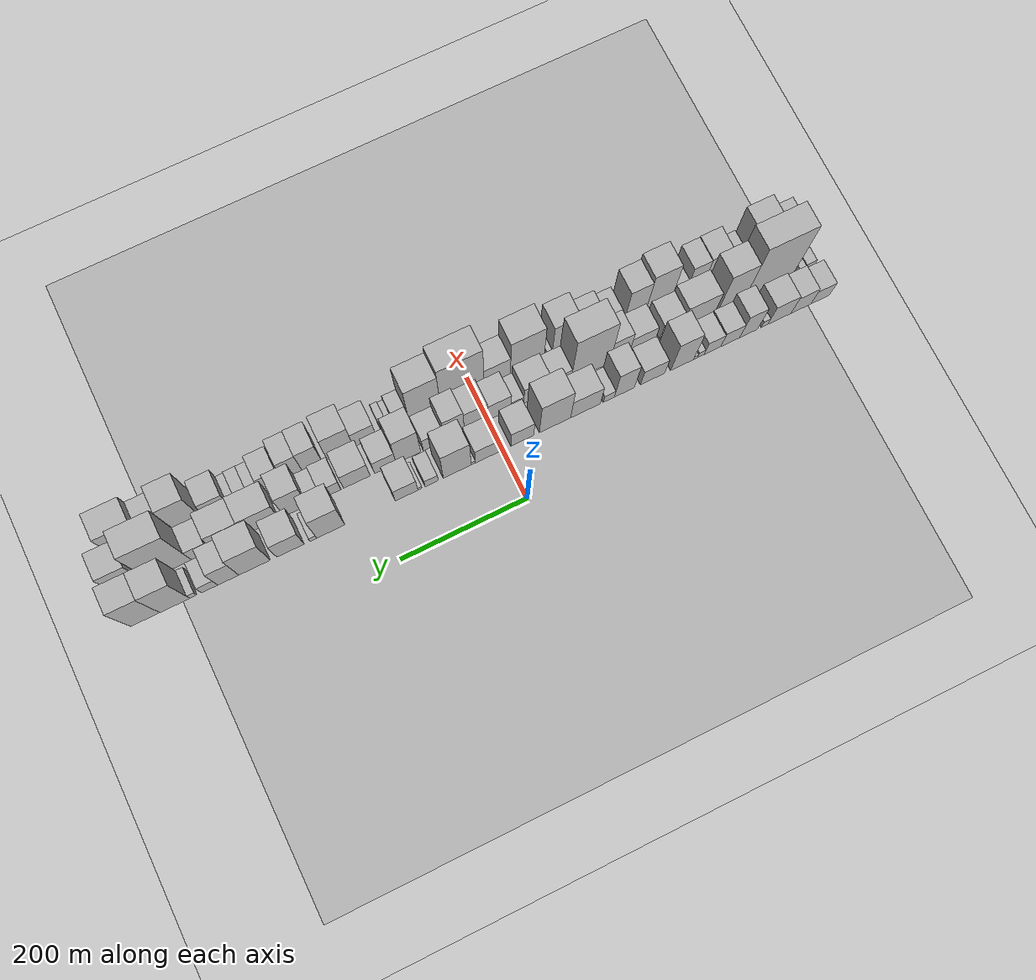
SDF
<?xml version="1.0" encoding="utf-8"?>

<sdf version="1.6">

   <world name="default">

      <gui fullscreen="0">

         <camera name="user_camera">

            <pose>-15 0 4.57585 0 0 0</pose>

            <view_controller>orbit</view_controller>

         </camera>

      </gui>

      <scene>

         <sky>

           <clouds>

             <speed>12</speed>

           </clouds>

         </sky>

         <ambient>0.4 0.4 0.4 1</ambient>

         <background>0.7 0.7 0.7 1</background>

         <shadows>1</shadows>

      </scene>

      <gravity>0 0 -9.8066</gravity>

      <magnetic_field>6e-06 2.3e-05 -4.2e-05</magnetic_field>

      <physics default="0" name="default_physics" type="ode">

         <ode>

            <solver>

               <type>quick</type>

               <iters>10</iters>

               <sor>1.0</sor>

               <use_dynamic_moi_rescaling>0</use_dynamic_moi_rescaling>

            </solver>

            <constraints>

               <cfm>0</cfm>

               <erp>0.2</erp>

               <contact_max_correcting_vel>100</contact_max_correcting_vel>

               <contact_surface_layer>0.001</contact_surface_layer>

            </constraints>

         </ode>

         <max_step_size>0.004</max_step_size>

         <real_time_factor>1</real_time_factor>

         <real_time_update_rate>250</real_time_update_rate>

      </physics>

      <light name="sun" type="directional">

         <cast_shadows>1</cast_shadows>

         <pose>0 0 10 0 0 0</pose>

         <diffuse>0.8 0.8 0.8 1</diffuse>

         <specular>0.2 0.2 0.2 1</specular>

         <attenuation>

            <range>1000</range>

            <constant>0.9</constant>

            <linear>0.01</linear>

            <quadratic>0.001</quadratic>

         </attenuation>

         <direction>-0.5 0.1 -0.9</direction>

      </light>

      <include>

         <name>ground_plane_1</name>

         <uri>model://HANNAS_ground_plane</uri>

         <pose>0 0 0  0 0 0</pose>

      </include>

      <include>

         <name>ground_plane_2</name>

         <uri>model://HANNAS_ground_plane</uri>

         <pose>100 0 0  0 0 0</pose>

      </include>

      <model name="building_1">

         <static>1</static>

         <pose frame="">100.0000 -520.5226 0 0.000000 0.000000 0.000000</pose>

         <link name="link">

            <pose frame="">0 0 27.00 0 0 0</pose>

            <collision name="collision">

               <geometry>

                  <box>

                     <size>40.0000 30.9549 54.0000</size>

                  </box>

               </geometry>

               <max_contacts>10</max_contacts>

               <surface>

                  <contact>

                     <ode/>

                  </contact>

                  <bounce/>

                  <friction>

                     <torsional>

                        <ode/>

                     </torsional>

                     <ode/>

                  </friction>

               </surface>

            </collision>

            <visual name="visual">

               <cast_shadows>0</cast_shadows>

               <geometry>

                  <box>

                     <size>40.0000 30.9549 54.0000</size>

                  </box>

               </geometry>

               <material>

                  <script>

                     <uri>model://HANNAS_wall/materials/scripts</uri>

                     <uri>model://HANNAS_wall/materials/textures</uri>

                     <name>vrc/HANNAS_wall</name>

                  </script>

               </material>

            </visual>

            <self_collide>0</self_collide>

            <enable_wind>0</enable_wind>

            <kinematic>0</kinematic>

         </link>

      </model>

      <model name="building_2">

         <static>1</static>

         <pose frame="">100.0000 -488.2523 0 0.000000 0.000000 0.000000</pose>

         <link name="link">

            <pose frame="">0 0 33.00 0 0 0</pose>

            <collision name="collision">

               <geometry>

                  <box>

                     <size>40.0000 33.5855 66.0000</size>

                  </box>

               </geometry>

               <max_contacts>10</max_contacts>

               <surface>

                  <contact>

                     <ode/>

                  </contact>

                  <bounce/>

                  <friction>

                     <torsional>

                        <ode/>

                     </torsional>

                     <ode/>

                  </friction>

               </surface>

            </collision>

            <visual name="visual">

               <cast_shadows>0</cast_shadows>

               <geometry>

                  <box>

                     <size>40.0000 33.5855 66.0000</size>

                  </box>

               </geometry>

               <material>

                  <script>

                     <uri>model://HANNAS_wall/materials/scripts</uri>

                     <uri>model://HANNAS_wall/materials/textures</uri>

                     <name>vrc/HANNAS_wall</name>

                  </script>

               </material>

            </visual>

            <self_collide>0</self_collide>

            <enable_wind>0</enable_wind>

            <kinematic>0</kinematic>

         </link>

      </model>

      <model name="building_3">

         <static>1</static>

         <pose frame="">100.0000 -452.0912 0 0.000000 0.000000 0.000000</pose>

         <link name="link">

            <pose frame="">0 0 37.50 0 0 0</pose>

            <collision name="collision">

               <geometry>

                  <box>

                     <size>40.0000 38.7367 75.0000</size>

                  </box>

               </geometry>

               <max_contacts>10</max_contacts>

               <surface>

                  <contact>

                     <ode/>

                  </contact>

                  <bounce/>

                  <friction>

                     <torsional>

                        <ode/>

                     </torsional>

                     <ode/>

                  </friction>

               </surface>

            </collision>

            <visual name="visual">

               <cast_shadows>0</cast_shadows>

               <geometry>

                  <box>

                     <size>40.0000 38.7367 75.0000</size>

                  </box>

               </geometry>

               <material>

                  <script>

                     <uri>model://HANNAS_wall/materials/scripts</uri>

                     <uri>model://HANNAS_wall/materials/textures</uri>

                     <name>vrc/HANNAS_wall</name>

                  </script>

               </material>

            </visual>

            <self_collide>0</self_collide>

            <enable_wind>0</enable_wind>

            <kinematic>0</kinematic>

         </link>

      </model>

      <model name="building_4">

         <static>1</static>

         <pose frame="">100.0000 -427.2255 0 0.000000 0.000000 0.000000</pose>

         <link name="link">

            <pose frame="">0 0 13.50 0 0 0</pose>

            <collision name="collision">

               <geometry>

                  <box>

                     <size>40.0000 10.9949 27.0000</size>

                  </box>

               </geometry>

               <max_contacts>10</max_contacts>

               <surface>

                  <contact>

                     <ode/>

                  </contact>

                  <bounce/>

                  <friction>

                     <torsional>

                        <ode/>

                     </torsional>

                     <ode/>

                  </friction>

               </surface>

            </collision>

            <visual name="visual">

               <cast_shadows>0</cast_shadows>

               <geometry>

                  <box>

                     <size>40.0000 10.9949 27.0000</size>

                  </box>

               </geometry>

               <material>

                  <script>

                     <uri>model://HANNAS_wall/materials/scripts</uri>

                     <uri>model://HANNAS_wall/materials/textures</uri>

                     <name>vrc/HANNAS_wall</name>

                  </script>

               </material>

            </visual>

            <self_collide>0</self_collide>

            <enable_wind>0</enable_wind>

            <kinematic>0</kinematic>

         </link>

      </model>

      <model name="building_5">

         <static>1</static>

         <pose frame="">100.0000 -400.7128 0 0.000000 0.000000 0.000000</pose>

         <link name="link">

            <pose frame="">0 0 46.50 0 0 0</pose>

            <collision name="collision">

               <geometry>

                  <box>

                     <size>40.0000 30.0306 93.0000</size>

                  </box>

               </geometry>

               <max_contacts>10</max_contacts>

               <surface>

                  <contact>

                     <ode/>

                  </contact>

                  <bounce/>

                  <friction>

                     <torsional>

                        <ode/>

                     </torsional>

                     <ode/>

                  </friction>

               </surface>

            </collision>

            <visual name="visual">

               <cast_shadows>0</cast_shadows>

               <geometry>

                  <box>

                     <size>40.0000 30.0306 93.0000</size>

                  </box>

               </geometry>

               <material>

                  <script>

                     <uri>model://HANNAS_wall/materials/scripts</uri>

                     <uri>model://HANNAS_wall/materials/textures</uri>

                     <name>vrc/HANNAS_wall</name>

                  </script>

               </material>

            </visual>

            <self_collide>0</self_collide>

            <enable_wind>0</enable_wind>

            <kinematic>0</kinematic>

         </link>

      </model>

      <model name="building_6">

         <static>1</static>

         <pose frame="">100.0000 -370.0675 0 0.000000 0.000000 0.000000</pose>

         <link name="link">

            <pose frame="">0 0 30.00 0 0 0</pose>

            <collision name="collision">

               <geometry>

                  <box>

                     <size>40.0000 31.2598 60.0000</size>

                  </box>

               </geometry>

               <max_contacts>10</max_contacts>

               <surface>

                  <contact>

                     <ode/>

                  </contact>

                  <bounce/>

                  <friction>

                     <torsional>

                        <ode/>

                     </torsional>

                     <ode/>

                  </friction>

               </surface>

            </collision>

            <visual name="visual">

               <cast_shadows>0</cast_shadows>

               <geometry>

                  <box>

                     <size>40.0000 31.2598 60.0000</size>

                  </box>

               </geometry>

               <material>

                  <script>

                     <uri>model://HANNAS_wall/materials/scripts</uri>

                     <uri>model://HANNAS_wall/materials/textures</uri>

                     <name>vrc/HANNAS_wall</name>

                  </script>

               </material>

            </visual>

            <self_collide>0</self_collide>

            <enable_wind>0</enable_wind>

            <kinematic>0</kinematic>

         </link>

      </model>

      <model name="building_7">

         <static>1</static>

         <pose frame="">100.0000 -340.5071 0 0.000000 0.000000 0.000000</pose>

         <link name="link">

            <pose frame="">0 0 27.00 0 0 0</pose>

            <collision name="collision">

               <geometry>

                  <box>

                     <size>40.0000 27.8611 54.0000</size>

                  </box>

               </geometry>

               <max_contacts>10</max_contacts>

               <surface>

                  <contact>

                     <ode/>

                  </contact>

                  <bounce/>

                  <friction>

                     <torsional>

                        <ode/>

                     </torsional>

                     <ode/>

                  </friction>

               </surface>

            </collision>

            <visual name="visual">

               <cast_shadows>0</cast_shadows>

               <geometry>

                  <box>

                     <size>40.0000 27.8611 54.0000</size>

                  </box>

               </geometry>

               <material>

                  <script>

                     <uri>model://HANNAS_wall/materials/scripts</uri>

                     <uri>model://HANNAS_wall/materials/textures</uri>

                     <name>vrc/HANNAS_wall</name>

                  </script>

               </material>

            </visual>

            <self_collide>0</self_collide>

            <enable_wind>0</enable_wind>

            <kinematic>0</kinematic>

         </link>

      </model>

      <model name="building_8">

         <static>1</static>

         <pose frame="">100.0000 -321.2389 0 0.000000 0.000000 0.000000</pose>

         <link name="link">

            <pose frame="">0 0 12.00 0 0 0</pose>

            <collision name="collision">

               <geometry>

                  <box>

                     <size>40.0000 10.6752 24.0000</size>

                  </box>

               </geometry>

               <max_contacts>10</max_contacts>

               <surface>

                  <contact>

                     <ode/>

                  </contact>

                  <bounce/>

                  <friction>

                     <torsional>

                        <ode/>

                     </torsional>

                     <ode/>

                  </friction>

               </surface>

            </collision>

            <visual name="visual">

               <cast_shadows>0</cast_shadows>

               <geometry>

                  <box>

                     <size>40.0000 10.6752 24.0000</size>

                  </box>

               </geometry>

               <material>

                  <script>

                     <uri>model://HANNAS_wall/materials/scripts</uri>

                     <uri>model://HANNAS_wall/materials/textures</uri>

                     <name>vrc/HANNAS_wall</name>

                  </script>

               </material>

            </visual>

            <self_collide>0</self_collide>

            <enable_wind>0</enable_wind>

            <kinematic>0</kinematic>

         </link>

      </model>

      <model name="building_9">

         <static>1</static>

         <pose frame="">100.0000 -312.6179 0 0.000000 0.000000 0.000000</pose>

         <link name="link">

            <pose frame="">0 0 7.50 0 0 0</pose>

            <collision name="collision">

               <geometry>

                  <box>

                     <size>40.0000 6.5669 15.0000</size>

                  </box>

               </geometry>

               <max_contacts>10</max_contacts>

               <surface>

                  <contact>

                     <ode/>

                  </contact>

                  <bounce/>

                  <friction>

                     <torsional>

                        <ode/>

                     </torsional>

                     <ode/>

                  </friction>

               </surface>

            </collision>

            <visual name="visual">

               <cast_shadows>0</cast_shadows>

               <geometry>

                  <box>

                     <size>40.0000 6.5669 15.0000</size>

                  </box>

               </geometry>

               <material>

                  <script>

                     <uri>model://HANNAS_wall/materials/scripts</uri>

                     <uri>model://HANNAS_wall/materials/textures</uri>

                     <name>vrc/HANNAS_wall</name>

                  </script>

               </material>

            </visual>

            <self_collide>0</self_collide>

            <enable_wind>0</enable_wind>

            <kinematic>0</kinematic>

         </link>

      </model>

      <model name="building_10">

         <static>1</static>

         <pose frame="">100.0000 -290.5077 0 0.000000 0.000000 0.000000</pose>

         <link name="link">

            <pose frame="">0 0 60.00 0 0 0</pose>

            <collision name="collision">

               <geometry>

                  <box>

                     <size>40.0000 37.6535 120.0000</size>

                  </box>

               </geometry>

               <max_contacts>10</max_contacts>

               <surface>

                  <contact>

                     <ode/>

                  </contact>

                  <bounce/>

                  <friction>

                     <torsional>

                        <ode/>

                     </torsional>

                     <ode/>

                  </friction>

               </surface>

            </collision>

            <visual name="visual">

               <cast_shadows>0</cast_shadows>

               <geometry>

                  <box>

                     <size>40.0000 37.6535 120.0000</size>

                  </box>

               </geometry>

               <material>

                  <script>

                     <uri>model://HANNAS_wall/materials/scripts</uri>

                     <uri>model://HANNAS_wall/materials/textures</uri>

                     <name>vrc/HANNAS_wall</name>

                  </script>

               </material>

            </visual>

            <self_collide>0</self_collide>

            <enable_wind>0</enable_wind>

            <kinematic>0</kinematic>

         </link>

      </model>

      <model name="building_11">

         <static>1</static>

         <pose frame="">100.0000 -241.9130 0 0.000000 0.000000 0.000000</pose>

         <link name="link">

            <pose frame="">0 0 33.00 0 0 0</pose>

            <collision name="collision">

               <geometry>

                  <box>

                     <size>40.0000 39.5359 66.0000</size>

                  </box>

               </geometry>

               <max_contacts>10</max_contacts>

               <surface>

                  <contact>

                     <ode/>

                  </contact>

                  <bounce/>

                  <friction>

                     <torsional>

                        <ode/>

                     </torsional>

                     <ode/>

                  </friction>

               </surface>

            </collision>

            <visual name="visual">

               <cast_shadows>0</cast_shadows>

               <geometry>

                  <box>

                     <size>40.0000 39.5359 66.0000</size>

                  </box>

               </geometry>

               <material>

                  <script>

                     <uri>model://HANNAS_wall/materials/scripts</uri>

                     <uri>model://HANNAS_wall/materials/textures</uri>

                     <name>vrc/HANNAS_wall</name>

                  </script>

               </material>

            </visual>

            <self_collide>0</self_collide>

            <enable_wind>0</enable_wind>

            <kinematic>0</kinematic>

         </link>

      </model>

      <model name="building_12">

         <static>1</static>

         <pose frame="">100.0000 -195.8661 0 0.000000 0.000000 0.000000</pose>

         <link name="link">

            <pose frame="">0 0 54.00 0 0 0</pose>

            <collision name="collision">

               <geometry>

                  <box>

                     <size>40.0000 32.5578 108.0000</size>

                  </box>

               </geometry>

               <max_contacts>10</max_contacts>

               <surface>

                  <contact>

                     <ode/>

                  </contact>

                  <bounce/>

                  <friction>

                     <torsional>

                        <ode/>

                     </torsional>

                     <ode/>

                  </friction>

               </surface>

            </collision>

            <visual name="visual">

               <cast_shadows>0</cast_shadows>

               <geometry>

                  <box>

                     <size>40.0000 32.5578 108.0000</size>

                  </box>

               </geometry>

               <material>

                  <script>

                     <uri>model://HANNAS_wall/materials/scripts</uri>

                     <uri>model://HANNAS_wall/materials/textures</uri>

                     <name>vrc/HANNAS_wall</name>

                  </script>

               </material>

            </visual>

            <self_collide>0</self_collide>

            <enable_wind>0</enable_wind>

            <kinematic>0</kinematic>

         </link>

      </model>

      <model name="building_13">

         <static>1</static>

         <pose frame="">100.0000 -170.6438 0 0.000000 0.000000 0.000000</pose>

         <link name="link">

            <pose frame="">0 0 16.50 0 0 0</pose>

            <collision name="collision">

               <geometry>

                  <box>

                     <size>40.0000 17.8870 33.0000</size>

                  </box>

               </geometry>

               <max_contacts>10</max_contacts>

               <surface>

                  <contact>

                     <ode/>

                  </contact>

                  <bounce/>

                  <friction>

                     <torsional>

                        <ode/>

                     </torsional>

                     <ode/>

                  </friction>

               </surface>

            </collision>

            <visual name="visual">

               <cast_shadows>0</cast_shadows>

               <geometry>

                  <box>

                     <size>40.0000 17.8870 33.0000</size>

                  </box>

               </geometry>

               <material>

                  <script>

                     <uri>model://HANNAS_wall/materials/scripts</uri>

                     <uri>model://HANNAS_wall/materials/textures</uri>

                     <name>vrc/HANNAS_wall</name>

                  </script>

               </material>

            </visual>

            <self_collide>0</self_collide>

            <enable_wind>0</enable_wind>

            <kinematic>0</kinematic>

         </link>

      </model>

      <model name="building_14">

         <static>1</static>

         <pose frame="">100.0000 -132.5002 0 0.000000 0.000000 0.000000</pose>

         <link name="link">

            <pose frame="">0 0 42.00 0 0 0</pose>

            <collision name="collision">

               <geometry>

                  <box>

                     <size>40.0000 48.4001 84.0000</size>

                  </box>

               </geometry>

               <max_contacts>10</max_contacts>

               <surface>

                  <contact>

                     <ode/>

                  </contact>

                  <bounce/>

                  <friction>

                     <torsional>

                        <ode/>

                     </torsional>

                     <ode/>

                  </friction>

               </surface>

            </collision>

            <visual name="visual">

               <cast_shadows>0</cast_shadows>

               <geometry>

                  <box>

                     <size>40.0000 48.4001 84.0000</size>

                  </box>

               </geometry>

               <material>

                  <script>

                     <uri>model://HANNAS_wall/materials/scripts</uri>

                     <uri>model://HANNAS_wall/materials/textures</uri>

                     <name>vrc/HANNAS_wall</name>

                  </script>

               </material>

            </visual>

            <self_collide>0</self_collide>

            <enable_wind>0</enable_wind>

            <kinematic>0</kinematic>

         </link>

      </model>

      <model name="building_15">

         <static>1</static>

         <pose frame="">100.0000 -83.1058 0 0.000000 0.000000 0.000000</pose>

         <link name="link">

            <pose frame="">0 0 69.00 0 0 0</pose>

            <collision name="collision">

               <geometry>

                  <box>

                     <size>40.0000 50.3887 138.0000</size>

                  </box>

               </geometry>

               <max_contacts>10</max_contacts>

               <surface>

                  <contact>

                     <ode/>

                  </contact>

                  <bounce/>

                  <friction>

                     <torsional>

                        <ode/>

                     </torsional>

                     <ode/>

                  </friction>

               </surface>

            </collision>

            <visual name="visual">

               <cast_shadows>0</cast_shadows>

               <geometry>

                  <box>

                     <size>40.0000 50.3887 138.0000</size>

                  </box>

               </geometry>

               <material>

                  <script>

                     <uri>model://HANNAS_wall/materials/scripts</uri>

                     <uri>model://HANNAS_wall/materials/textures</uri>

                     <name>vrc/HANNAS_wall</name>

                  </script>

               </material>

            </visual>

            <self_collide>0</self_collide>

            <enable_wind>0</enable_wind>

            <kinematic>0</kinematic>

         </link>

      </model>

      <model name="building_16">

         <static>1</static>

         <pose frame="">100.0000 -30.5629 0 0.000000 0.000000 0.000000</pose>

         <link name="link">

            <pose frame="">0 0 34.50 0 0 0</pose>

            <collision name="collision">

               <geometry>

                  <box>

                     <size>40.0000 36.6970 69.0000</size>

                  </box>

               </geometry>

               <max_contacts>10</max_contacts>

               <surface>

                  <contact>

                     <ode/>

                  </contact>

                  <bounce/>

                  <friction>

                     <torsional>

                        <ode/>

                     </torsional>

                     <ode/>

                  </friction>

               </surface>

            </collision>

            <visual name="visual">

               <cast_shadows>0</cast_shadows>

               <geometry>

                  <box>

                     <size>40.0000 36.6970 69.0000</size>

                  </box>

               </geometry>

               <material>

                  <script>

                     <uri>model://HANNAS_wall/materials/scripts</uri>

                     <uri>model://HANNAS_wall/materials/textures</uri>

                     <name>vrc/HANNAS_wall</name>

                  </script>

               </material>

            </visual>

            <self_collide>0</self_collide>

            <enable_wind>0</enable_wind>

            <kinematic>0</kinematic>

         </link>

      </model>

      <model name="building_17">

         <static>1</static>

         <pose frame="">100.0000 1.1108 0 0.000000 0.000000 0.000000</pose>

         <link name="link">

            <pose frame="">0 0 7.50 0 0 0</pose>

            <collision name="collision">

               <geometry>

                  <box>

                     <size>40.0000 6.6503 15.0000</size>

                  </box>

               </geometry>

               <max_contacts>10</max_contacts>

               <surface>

                  <contact>

                     <ode/>

                  </contact>

                  <bounce/>

                  <friction>

                     <torsional>

                        <ode/>

                     </torsional>

                     <ode/>

                  </friction>

               </surface>

            </collision>

            <visual name="visual">

               <cast_shadows>0</cast_shadows>

               <geometry>

                  <box>

                     <size>40.0000 6.6503 15.0000</size>

                  </box>

               </geometry>

               <material>

                  <script>

                     <uri>model://HANNAS_wall/materials/scripts</uri>

                     <uri>model://HANNAS_wall/materials/textures</uri>

                     <name>vrc/HANNAS_wall</name>

                  </script>

               </material>

            </visual>

            <self_collide>0</self_collide>

            <enable_wind>0</enable_wind>

            <kinematic>0</kinematic>

         </link>

      </model>

      <model name="building_18">

         <static>1</static>

         <pose frame="">100.0000 24.4933 0 0.000000 0.000000 0.000000</pose>

         <link name="link">

            <pose frame="">0 0 34.50 0 0 0</pose>

            <collision name="collision">

               <geometry>

                  <box>

                     <size>40.0000 40.1148 69.0000</size>

                  </box>

               </geometry>

               <max_contacts>10</max_contacts>

               <surface>

                  <contact>

                     <ode/>

                  </contact>

                  <bounce/>

                  <friction>

                     <torsional>

                        <ode/>

                     </torsional>

                     <ode/>

                  </friction>

               </surface>

            </collision>

            <visual name="visual">

               <cast_shadows>0</cast_shadows>

               <geometry>

                  <box>

                     <size>40.0000 40.1148 69.0000</size>

                  </box>

               </geometry>

               <material>

                  <script>

                     <uri>model://HANNAS_wall/materials/scripts</uri>

                     <uri>model://HANNAS_wall/materials/textures</uri>

                     <name>vrc/HANNAS_wall</name>

                  </script>

               </material>

            </visual>

            <self_collide>0</self_collide>

            <enable_wind>0</enable_wind>

            <kinematic>0</kinematic>

         </link>

      </model>

      <model name="building_19">

         <static>1</static>

         <pose frame="">100.0000 47.8376 0 0.000000 0.000000 0.000000</pose>

         <link name="link">

            <pose frame="">0 0 7.50 0 0 0</pose>

            <collision name="collision">

               <geometry>

                  <box>

                     <size>40.0000 6.5738 15.0000</size>

                  </box>

               </geometry>

               <max_contacts>10</max_contacts>

               <surface>

                  <contact>

                     <ode/>

                  </contact>

                  <bounce/>

                  <friction>

                     <torsional>

                        <ode/>

                     </torsional>

                     <ode/>

                  </friction>

               </surface>

            </collision>

            <visual name="visual">

               <cast_shadows>0</cast_shadows>

               <geometry>

                  <box>

                     <size>40.0000 6.5738 15.0000</size>

                  </box>

               </geometry>

               <material>

                  <script>

                     <uri>model://HANNAS_wall/materials/scripts</uri>

                     <uri>model://HANNAS_wall/materials/textures</uri>

                     <name>vrc/HANNAS_wall</name>

                  </script>

               </material>

            </visual>

            <self_collide>0</self_collide>

            <enable_wind>0</enable_wind>

            <kinematic>0</kinematic>

         </link>

      </model>

      <model name="building_20">

         <static>1</static>

         <pose frame="">100.0000 73.2737 0 0.000000 0.000000 0.000000</pose>

         <link name="link">

            <pose frame="">0 0 64.50 0 0 0</pose>

            <collision name="collision">

               <geometry>

                  <box>

                     <size>40.0000 44.2983 129.0000</size>

                  </box>

               </geometry>

               <max_contacts>10</max_contacts>

               <surface>

                  <contact>

                     <ode/>

                  </contact>

                  <bounce/>

                  <friction>

                     <torsional>

                        <ode/>

                     </torsional>

                     <ode/>

                  </friction>

               </surface>

            </collision>

            <visual name="visual">

               <cast_shadows>0</cast_shadows>

               <geometry>

                  <box>

                     <size>40.0000 44.2983 129.0000</size>

                  </box>

               </geometry>

               <material>

                  <script>

                     <uri>model://HANNAS_wall/materials/scripts</uri>

                     <uri>model://HANNAS_wall/materials/textures</uri>

                     <name>vrc/HANNAS_wall</name>

                  </script>

               </material>

            </visual>

            <self_collide>0</self_collide>

            <enable_wind>0</enable_wind>

            <kinematic>0</kinematic>

         </link>

      </model>

      <model name="building_21">

         <static>1</static>

         <pose frame="">100.0000 113.8179 0 0.000000 0.000000 0.000000</pose>

         <link name="link">

            <pose frame="">0 0 18.00 0 0 0</pose>

            <collision name="collision">

               <geometry>

                  <box>

                     <size>40.0000 20.7900 36.0000</size>

                  </box>

               </geometry>

               <max_contacts>10</max_contacts>

               <surface>

                  <contact>

                     <ode/>

                  </contact>

                  <bounce/>

                  <friction>

                     <torsional>

                        <ode/>

                     </torsional>

                     <ode/>

                  </friction>

               </surface>

            </collision>

            <visual name="visual">

               <cast_shadows>0</cast_shadows>

               <geometry>

                  <box>

                     <size>40.0000 20.7900 36.0000</size>

                  </box>

               </geometry>

               <material>

                  <script>

                     <uri>model://HANNAS_wall/materials/scripts</uri>

                     <uri>model://HANNAS_wall/materials/textures</uri>

                     <name>vrc/HANNAS_wall</name>

                  </script>

               </material>

            </visual>

            <self_collide>0</self_collide>

            <enable_wind>0</enable_wind>

            <kinematic>0</kinematic>

         </link>

      </model>

      <model name="building_22">

         <static>1</static>

         <pose frame="">100.0000 132.3706 0 0.000000 0.000000 0.000000</pose>

         <link name="link">

            <pose frame="">0 0 7.50 0 0 0</pose>

            <collision name="collision">

               <geometry>

                  <box>

                     <size>40.0000 6.3154 15.0000</size>

                  </box>

               </geometry>

               <max_contacts>10</max_contacts>

               <surface>

                  <contact>

                     <ode/>

                  </contact>

                  <bounce/>

                  <friction>

                     <torsional>

                        <ode/>

                     </torsional>

                     <ode/>

                  </friction>

               </surface>

            </collision>

            <visual name="visual">

               <cast_shadows>0</cast_shadows>

               <geometry>

                  <box>

                     <size>40.0000 6.3154 15.0000</size>

                  </box>

               </geometry>

               <material>

                  <script>

                     <uri>model://HANNAS_wall/materials/scripts</uri>

                     <uri>model://HANNAS_wall/materials/textures</uri>

                     <name>vrc/HANNAS_wall</name>

                  </script>

               </material>

            </visual>

            <self_collide>0</self_collide>

            <enable_wind>0</enable_wind>

            <kinematic>0</kinematic>

         </link>

      </model>

      <model name="building_23">

         <static>1</static>

         <pose frame="">100.0000 153.3923 0 0.000000 0.000000 0.000000</pose>

         <link name="link">

            <pose frame="">0 0 31.50 0 0 0</pose>

            <collision name="collision">

               <geometry>

                  <box>

                     <size>40.0000 35.7281 63.0000</size>

                  </box>

               </geometry>

               <max_contacts>10</max_contacts>

               <surface>

                  <contact>

                     <ode/>

                  </contact>

                  <bounce/>

                  <friction>

                     <torsional>

                        <ode/>

                     </torsional>

                     <ode/>

                  </friction>

               </surface>

            </collision>

            <visual name="visual">

               <cast_shadows>0</cast_shadows>

               <geometry>

                  <box>

                     <size>40.0000 35.7281 63.0000</size>

                  </box>

               </geometry>

               <material>

                  <script>

                     <uri>model://HANNAS_wall/materials/scripts</uri>

                     <uri>model://HANNAS_wall/materials/textures</uri>

                     <name>vrc/HANNAS_wall</name>

                  </script>

               </material>

            </visual>

            <self_collide>0</self_collide>

            <enable_wind>0</enable_wind>

            <kinematic>0</kinematic>

         </link>

      </model>

      <model name="building_24">

         <static>1</static>

         <pose frame="">100.0000 272.0891 0 0.000000 0.000000 0.000000</pose>

         <link name="link">

            <pose frame="">0 0 60.00 0 0 0</pose>

            <collision name="collision">

               <geometry>

                  <box>

                     <size>40.0000 43.8885 120.0000</size>

                  </box>

               </geometry>

               <max_contacts>10</max_contacts>

               <surface>

                  <contact>

                     <ode/>

                  </contact>

                  <bounce/>

                  <friction>

                     <torsional>

                        <ode/>

                     </torsional>

                     <ode/>

                  </friction>

               </surface>

            </collision>

            <visual name="visual">

               <cast_shadows>0</cast_shadows>

               <geometry>

                  <box>

                     <size>40.0000 43.8885 120.0000</size>

                  </box>

               </geometry>

               <material>

                  <script>

                     <uri>model://HANNAS_wall/materials/scripts</uri>

                     <uri>model://HANNAS_wall/materials/textures</uri>

                     <name>vrc/HANNAS_wall</name>

                  </script>

               </material>

            </visual>

            <self_collide>0</self_collide>

            <enable_wind>0</enable_wind>

            <kinematic>0</kinematic>

         </link>

      </model>

      <model name="building_25">

         <static>1</static>

         <pose frame="">100.0000 299.2627 0 0.000000 0.000000 0.000000</pose>

         <link name="link">

            <pose frame="">0 0 10.50 0 0 0</pose>

            <collision name="collision">

               <geometry>

                  <box>

                     <size>40.0000 10.4587 21.0000</size>

                  </box>

               </geometry>

               <max_contacts>10</max_contacts>

               <surface>

                  <contact>

                     <ode/>

                  </contact>

                  <bounce/>

                  <friction>

                     <torsional>

                        <ode/>

                     </torsional>

                     <ode/>

                  </friction>

               </surface>

            </collision>

            <visual name="visual">

               <cast_shadows>0</cast_shadows>

               <geometry>

                  <box>

                     <size>40.0000 10.4587 21.0000</size>

                  </box>

               </geometry>

               <material>

                  <script>

                     <uri>model://HANNAS_wall/materials/scripts</uri>

                     <uri>model://HANNAS_wall/materials/textures</uri>

                     <name>vrc/HANNAS_wall</name>

                  </script>

               </material>

            </visual>

            <self_collide>0</self_collide>

            <enable_wind>0</enable_wind>

            <kinematic>0</kinematic>

         </link>

      </model>

      <model name="building_26">

         <static>1</static>

         <pose frame="">100.0000 334.7505 0 0.000000 0.000000 0.000000</pose>

         <link name="link">

            <pose frame="">0 0 42.00 0 0 0</pose>

            <collision name="collision">

               <geometry>

                  <box>

                     <size>40.0000 42.5169 84.0000</size>

                  </box>

               </geometry>

               <max_contacts>10</max_contacts>

               <surface>

                  <contact>

                     <ode/>

                  </contact>

                  <bounce/>

                  <friction>

                     <torsional>

                        <ode/>

                     </torsional>

                     <ode/>

                  </friction>

               </surface>

            </collision>

            <visual name="visual">

               <cast_shadows>0</cast_shadows>

               <geometry>

                  <box>

                     <size>40.0000 42.5169 84.0000</size>

                  </box>

               </geometry>

               <material>

                  <script>

                     <uri>model://HANNAS_wall/materials/scripts</uri>

                     <uri>model://HANNAS_wall/materials/textures</uri>

                     <name>vrc/HANNAS_wall</name>

                  </script>

               </material>

            </visual>

            <self_collide>0</self_collide>

            <enable_wind>0</enable_wind>

            <kinematic>0</kinematic>

         </link>

      </model>

      <model name="building_27">

         <static>1</static>

         <pose frame="">100.0000 390.1884 0 0.000000 0.000000 0.000000</pose>

         <link name="link">

            <pose frame="">0 0 61.50 0 0 0</pose>

            <collision name="collision">

               <geometry>

                  <box>

                     <size>40.0000 48.3588 123.0000</size>

                  </box>

               </geometry>

               <max_contacts>10</max_contacts>

               <surface>

                  <contact>

                     <ode/>

                  </contact>

                  <bounce/>

                  <friction>

                     <torsional>

                        <ode/>

                     </torsional>

                     <ode/>

                  </friction>

               </surface>

            </collision>

            <visual name="visual">

               <cast_shadows>0</cast_shadows>

               <geometry>

                  <box>

                     <size>40.0000 48.3588 123.0000</size>

                  </box>

               </geometry>

               <material>

                  <script>

                     <uri>model://HANNAS_wall/materials/scripts</uri>

                     <uri>model://HANNAS_wall/materials/textures</uri>

                     <name>vrc/HANNAS_wall</name>

                  </script>

               </material>

            </visual>

            <self_collide>0</self_collide>

            <enable_wind>0</enable_wind>

            <kinematic>0</kinematic>

         </link>

      </model>

      <model name="building_28">

         <static>1</static>

         <pose frame="">100.0000 430.5338 0 0.000000 0.000000 0.000000</pose>

         <link name="link">

            <pose frame="">0 0 48.00 0 0 0</pose>

            <collision name="collision">

               <geometry>

                  <box>

                     <size>40.0000 32.3321 96.0000</size>

                  </box>

               </geometry>

               <max_contacts>10</max_contacts>

               <surface>

                  <contact>

                     <ode/>

                  </contact>

                  <bounce/>

                  <friction>

                     <torsional>

                        <ode/>

                     </torsional>

                     <ode/>

                  </friction>

               </surface>

            </collision>

            <visual name="visual">

               <cast_shadows>0</cast_shadows>

               <geometry>

                  <box>

                     <size>40.0000 32.3321 96.0000</size>

                  </box>

               </geometry>

               <material>

                  <script>

                     <uri>model://HANNAS_wall/materials/scripts</uri>

                     <uri>model://HANNAS_wall/materials/textures</uri>

                     <name>vrc/HANNAS_wall</name>

                  </script>

               </material>

            </visual>

            <self_collide>0</self_collide>

            <enable_wind>0</enable_wind>

            <kinematic>0</kinematic>

         </link>

      </model>

      <model name="building_29">

         <static>1</static>

         <pose frame="">100.0000 459.1189 0 0.000000 0.000000 0.000000</pose>

         <link name="link">

            <pose frame="">0 0 21.00 0 0 0</pose>

            <collision name="collision">

               <geometry>

                  <box>

                     <size>40.0000 24.8381 42.0000</size>

                  </box>

               </geometry>

               <max_contacts>10</max_contacts>

               <surface>

                  <contact>

                     <ode/>

                  </contact>

                  <bounce/>

                  <friction>

                     <torsional>

                        <ode/>

                     </torsional>

                     <ode/>

                  </friction>

               </surface>

            </collision>

            <visual name="visual">

               <cast_shadows>0</cast_shadows>

               <geometry>

                  <box>

                     <size>40.0000 24.8381 42.0000</size>

                  </box>

               </geometry>

               <material>

                  <script>

                     <uri>model://HANNAS_wall/materials/scripts</uri>

                     <uri>model://HANNAS_wall/materials/textures</uri>

                     <name>vrc/HANNAS_wall</name>

                  </script>

               </material>

            </visual>

            <self_collide>0</self_collide>

            <enable_wind>0</enable_wind>

            <kinematic>0</kinematic>

         </link>

      </model>

      <model name="building_30">

         <static>1</static>

         <pose frame="">100.0000 483.9694 0 0.000000 0.000000 0.000000</pose>

         <link name="link">

            <pose frame="">0 0 12.00 0 0 0</pose>

            <collision name="collision">

               <geometry>

                  <box>

                     <size>40.0000 10.8628 24.0000</size>

                  </box>

               </geometry>

               <max_contacts>10</max_contacts>

               <surface>

                  <contact>

                     <ode/>

                  </contact>

                  <bounce/>

                  <friction>

                     <torsional>

                        <ode/>

                     </torsional>

                     <ode/>

                  </friction>

               </surface>

            </collision>

            <visual name="visual">

               <cast_shadows>0</cast_shadows>

               <geometry>

                  <box>

                     <size>40.0000 10.8628 24.0000</size>

                  </box>

               </geometry>

               <material>

                  <script>

                     <uri>model://HANNAS_wall/materials/scripts</uri>

                     <uri>model://HANNAS_wall/materials/textures</uri>

                     <name>vrc/HANNAS_wall</name>

                  </script>

               </material>

            </visual>

            <self_collide>0</self_collide>

            <enable_wind>0</enable_wind>

            <kinematic>0</kinematic>

         </link>

      </model>

      <model name="building_31">

         <static>1</static>

         <pose frame="">100.0000 512.2028 0 0.000000 0.000000 0.000000</pose>

         <link name="link">

            <pose frame="">0 0 70.50 0 0 0</pose>

            <collision name="collision">

               <geometry>

                  <box>

                     <size>40.0000 45.6041 141.0000</size>

                  </box>

               </geometry>

               <max_contacts>10</max_contacts>

               <surface>

                  <contact>

                     <ode/>

                  </contact>

                  <bounce/>

                  <friction>

                     <torsional>

                        <ode/>

                     </torsional>

                     <ode/>

                  </friction>

               </surface>

            </collision>

            <visual name="visual">

               <cast_shadows>0</cast_shadows>

               <geometry>

                  <box>

                     <size>40.0000 45.6041 141.0000</size>

                  </box>

               </geometry>

               <material>

                  <script>

                     <uri>model://HANNAS_wall/materials/scripts</uri>

                     <uri>model://HANNAS_wall/materials/textures</uri>

                     <name>vrc/HANNAS_wall</name>

                  </script>

               </material>

            </visual>

            <self_collide>0</self_collide>

            <enable_wind>0</enable_wind>

            <kinematic>0</kinematic>

         </link>

      </model>

      <model name="building_32">

         <static>1</static>

         <pose frame="">100.0000 557.0036 0 0.000000 0.000000 0.000000</pose>

         <link name="link">

            <pose frame="">0 0 70.50 0 0 0</pose>

            <collision name="collision">

               <geometry>

                  <box>

                     <size>40.0000 43.9974 141.0000</size>

                  </box>

               </geometry>

               <max_contacts>10</max_contacts>

               <surface>

                  <contact>

                     <ode/>

                  </contact>

                  <bounce/>

                  <friction>

                     <torsional>

                        <ode/>

                     </torsional>

                     <ode/>

                  </friction>

               </surface>

            </collision>

            <visual name="visual">

               <cast_shadows>0</cast_shadows>

               <geometry>

                  <box>

                     <size>40.0000 43.9974 141.0000</size>

                  </box>

               </geometry>

               <material>

                  <script>

                     <uri>model://HANNAS_wall/materials/scripts</uri>

                     <uri>model://HANNAS_wall/materials/textures</uri>

                     <name>vrc/HANNAS_wall</name>

                  </script>

               </material>

            </visual>

            <self_collide>0</self_collide>

            <enable_wind>0</enable_wind>

            <kinematic>0</kinematic>

         </link>

      </model>

      <model name="building_33">

         <static>1</static>

         <pose frame="">149.0000 -527.3636 0 0.000000 0.000000 0.000000</pose>

         <link name="link">

            <pose frame="">0 0 15.00 0 0 0</pose>

            <collision name="collision">

               <geometry>

                  <box>

                     <size>40.0000 17.2728 30.0000</size>

                  </box>

               </geometry>

               <max_contacts>10</max_contacts>

               <surface>

                  <contact>

                     <ode/>

                  </contact>

                  <bounce/>

                  <friction>

                     <torsional>

                        <ode/>

                     </torsional>

                     <ode/>

                  </friction>

               </surface>

            </collision>

            <visual name="visual">

               <cast_shadows>0</cast_shadows>

               <geometry>

                  <box>

                     <size>40.0000 17.2728 30.0000</size>

                  </box>

               </geometry>

               <material>

                  <script>

                     <uri>model://HANNAS_wall/materials/scripts</uri>

                     <uri>model://HANNAS_wall/materials/textures</uri>

                     <name>vrc/HANNAS_wall</name>

                  </script>

               </material>

            </visual>

            <self_collide>0</self_collide>

            <enable_wind>0</enable_wind>

            <kinematic>0</kinematic>

         </link>

      </model>

      <model name="building_34">

         <static>1</static>

         <pose frame="">149.0000 -513.0328 0 0.000000 0.000000 0.000000</pose>

         <link name="link">

            <pose frame="">0 0 13.50 0 0 0</pose>

            <collision name="collision">

               <geometry>

                  <box>

                     <size>40.0000 11.3889 27.0000</size>

                  </box>

               </geometry>

               <max_contacts>10</max_contacts>

               <surface>

                  <contact>

                     <ode/>

                  </contact>

                  <bounce/>

                  <friction>

                     <torsional>

                        <ode/>

                     </torsional>

                     <ode/>

                  </friction>

               </surface>

            </collision>

            <visual name="visual">

               <cast_shadows>0</cast_shadows>

               <geometry>

                  <box>

                     <size>40.0000 11.3889 27.0000</size>

                  </box>

               </geometry>

               <material>

                  <script>

                     <uri>model://HANNAS_wall/materials/scripts</uri>

                     <uri>model://HANNAS_wall/materials/textures</uri>

                     <name>vrc/HANNAS_wall</name>

                  </script>

               </material>

            </visual>

            <self_collide>0</self_collide>

            <enable_wind>0</enable_wind>

            <kinematic>0</kinematic>

         </link>

      </model>

      <model name="building_35">

         <static>1</static>

         <pose frame="">149.0000 -458.8959 0 0.000000 0.000000 0.000000</pose>

         <link name="link">

            <pose frame="">0 0 102.00 0 0 0</pose>

            <collision name="collision">

               <geometry>

                  <box>

                     <size>40.0000 78.8850 204.0000</size>

                  </box>

               </geometry>

               <max_contacts>10</max_contacts>

               <surface>

                  <contact>

                     <ode/>

                  </contact>

                  <bounce/>

                  <friction>

                     <torsional>

                        <ode/>

                     </torsional>

                     <ode/>

                  </friction>

               </surface>

            </collision>

            <visual name="visual">

               <cast_shadows>0</cast_shadows>

               <geometry>

                  <box>

                     <size>40.0000 78.8850 204.0000</size>

                  </box>

               </geometry>

               <material>

                  <script>

                     <uri>model://HANNAS_wall/materials/scripts</uri>

                     <uri>model://HANNAS_wall/materials/textures</uri>

                     <name>vrc/HANNAS_wall</name>

                  </script>

               </material>

            </visual>

            <self_collide>0</self_collide>

            <enable_wind>0</enable_wind>

            <kinematic>0</kinematic>

         </link>

      </model>

      <model name="building_36">

         <static>1</static>

         <pose frame="">149.0000 -397.2426 0 0.000000 0.000000 0.000000</pose>

         <link name="link">

            <pose frame="">0 0 73.50 0 0 0</pose>

            <collision name="collision">

               <geometry>

                  <box>

                     <size>40.0000 44.4216 147.0000</size>

                  </box>

               </geometry>

               <max_contacts>10</max_contacts>

               <surface>

                  <contact>

                     <ode/>

                  </contact>

                  <bounce/>

                  <friction>

                     <torsional>

                        <ode/>

                     </torsional>

                     <ode/>

                  </friction>

               </surface>

            </collision>

            <visual name="visual">

               <cast_shadows>0</cast_shadows>

               <geometry>

                  <box>

                     <size>40.0000 44.4216 147.0000</size>

                  </box>

               </geometry>

               <material>

                  <script>

                     <uri>model://HANNAS_wall/materials/scripts</uri>

                     <uri>model://HANNAS_wall/materials/textures</uri>

                     <name>vrc/HANNAS_wall</name>

                  </script>

               </material>

            </visual>

            <self_collide>0</self_collide>

            <enable_wind>0</enable_wind>

            <kinematic>0</kinematic>

         </link>

      </model>

      <model name="building_37">

         <static>1</static>

         <pose frame="">149.0000 -343.1438 0 0.000000 0.000000 0.000000</pose>

         <link name="link">

            <pose frame="">0 0 45.00 0 0 0</pose>

            <collision name="collision">

               <geometry>

                  <box>

                     <size>40.0000 53.7761 90.0000</size>

                  </box>

               </geometry>

               <max_contacts>10</max_contacts>

               <surface>

                  <contact>

                     <ode/>

                  </contact>

                  <bounce/>

                  <friction>

                     <torsional>

                        <ode/>

                     </torsional>

                     <ode/>

                  </friction>

               </surface>

            </collision>

            <visual name="visual">

               <cast_shadows>0</cast_shadows>

               <geometry>

                  <box>

                     <size>40.0000 53.7761 90.0000</size>

                  </box>

               </geometry>

               <material>

                  <script>

                     <uri>model://HANNAS_wall/materials/scripts</uri>

                     <uri>model://HANNAS_wall/materials/textures</uri>

                     <name>vrc/HANNAS_wall</name>

                  </script>

               </material>

            </visual>

            <self_collide>0</self_collide>

            <enable_wind>0</enable_wind>

            <kinematic>0</kinematic>

         </link>

      </model>

      <model name="building_38">

         <static>1</static>

         <pose frame="">149.0000 -297.8388 0 0.000000 0.000000 0.000000</pose>

         <link name="link">

            <pose frame="">0 0 33.00 0 0 0</pose>

            <collision name="collision">

               <geometry>

                  <box>

                     <size>40.0000 36.8337 66.0000</size>

                  </box>

               </geometry>

               <max_contacts>10</max_contacts>

               <surface>

                  <contact>

                     <ode/>

                  </contact>

                  <bounce/>

                  <friction>

                     <torsional>

                        <ode/>

                     </torsional>

                     <ode/>

                  </friction>

               </surface>

            </collision>

            <visual name="visual">

               <cast_shadows>0</cast_shadows>

               <geometry>

                  <box>

                     <size>40.0000 36.8337 66.0000</size>

                  </box>

               </geometry>

               <material>

                  <script>

                     <uri>model://HANNAS_wall/materials/scripts</uri>

                     <uri>model://HANNAS_wall/materials/textures</uri>

                     <name>vrc/HANNAS_wall</name>

                  </script>

               </material>

            </visual>

            <self_collide>0</self_collide>

            <enable_wind>0</enable_wind>

            <kinematic>0</kinematic>

         </link>

      </model>

      <model name="building_39">

         <static>1</static>

         <pose frame="">149.0000 -249.7670 0 0.000000 0.000000 0.000000</pose>

         <link name="link">

            <pose frame="">0 0 34.50 0 0 0</pose>

            <collision name="collision">

               <geometry>

                  <box>

                     <size>40.0000 41.3099 69.0000</size>

                  </box>

               </geometry>

               <max_contacts>10</max_contacts>

               <surface>

                  <contact>

                     <ode/>

                  </contact>

                  <bounce/>

                  <friction>

                     <torsional>

                        <ode/>

                     </torsional>

                     <ode/>

                  </friction>

               </surface>

            </collision>

            <visual name="visual">

               <cast_shadows>0</cast_shadows>

               <geometry>

                  <box>

                     <size>40.0000 41.3099 69.0000</size>

                  </box>

               </geometry>

               <material>

                  <script>

                     <uri>model://HANNAS_wall/materials/scripts</uri>

                     <uri>model://HANNAS_wall/materials/textures</uri>

                     <name>vrc/HANNAS_wall</name>

                  </script>

               </material>

            </visual>

            <self_collide>0</self_collide>

            <enable_wind>0</enable_wind>

            <kinematic>0</kinematic>

         </link>

      </model>

      <model name="building_40">

         <static>1</static>

         <pose frame="">149.0000 -213.1885 0 0.000000 0.000000 0.000000</pose>

         <link name="link">

            <pose frame="">0 0 48.00 0 0 0</pose>

            <collision name="collision">

               <geometry>

                  <box>

                     <size>40.0000 31.8470 96.0000</size>

                  </box>

               </geometry>

               <max_contacts>10</max_contacts>

               <surface>

                  <contact>

                     <ode/>

                  </contact>

                  <bounce/>

                  <friction>

                     <torsional>

                        <ode/>

                     </torsional>

                     <ode/>

                  </friction>

               </surface>

            </collision>

            <visual name="visual">

               <cast_shadows>0</cast_shadows>

               <geometry>

                  <box>

                     <size>40.0000 31.8470 96.0000</size>

                  </box>

               </geometry>

               <material>

                  <script>

                     <uri>model://HANNAS_wall/materials/scripts</uri>

                     <uri>model://HANNAS_wall/materials/textures</uri>

                     <name>vrc/HANNAS_wall</name>

                  </script>

               </material>

            </visual>

            <self_collide>0</self_collide>

            <enable_wind>0</enable_wind>

            <kinematic>0</kinematic>

         </link>

      </model>

      <model name="building_41">

         <static>1</static>

         <pose frame="">149.0000 -165.3046 0 0.000000 0.000000 0.000000</pose>

         <link name="link">

            <pose frame="">0 0 93.00 0 0 0</pose>

            <collision name="collision">

               <geometry>

                  <box>

                     <size>40.0000 63.9208 186.0000</size>

                  </box>

               </geometry>

               <max_contacts>10</max_contacts>

               <surface>

                  <contact>

                     <ode/>

                  </contact>

                  <bounce/>

                  <friction>

                     <torsional>

                        <ode/>

                     </torsional>

                     <ode/>

                  </friction>

               </surface>

            </collision>

            <visual name="visual">

               <cast_shadows>0</cast_shadows>

               <geometry>

                  <box>

                     <size>40.0000 63.9208 186.0000</size>

                  </box>

               </geometry>

               <material>

                  <script>

                     <uri>model://HANNAS_wall/materials/scripts</uri>

                     <uri>model://HANNAS_wall/materials/textures</uri>

                     <name>vrc/HANNAS_wall</name>

                  </script>

               </material>

            </visual>

            <self_collide>0</self_collide>

            <enable_wind>0</enable_wind>

            <kinematic>0</kinematic>

         </link>

      </model>

      <model name="building_42">

         <static>1</static>

         <pose frame="">149.0000 -116.6130 0 0.000000 0.000000 0.000000</pose>

         <link name="link">

            <pose frame="">0 0 30.00 0 0 0</pose>

            <collision name="collision">

               <geometry>

                  <box>

                     <size>40.0000 33.4624 60.0000</size>

                  </box>

               </geometry>

               <max_contacts>10</max_contacts>

               <surface>

                  <contact>

                     <ode/>

                  </contact>

                  <bounce/>

                  <friction>

                     <torsional>

                        <ode/>

                     </torsional>

                     <ode/>

                  </friction>

               </surface>

            </collision>

            <visual name="visual">

               <cast_shadows>0</cast_shadows>

               <geometry>

                  <box>

                     <size>40.0000 33.4624 60.0000</size>

                  </box>

               </geometry>

               <material>

                  <script>

                     <uri>model://HANNAS_wall/materials/scripts</uri>

                     <uri>model://HANNAS_wall/materials/textures</uri>

                     <name>vrc/HANNAS_wall</name>

                  </script>

               </material>

            </visual>

            <self_collide>0</self_collide>

            <enable_wind>0</enable_wind>

            <kinematic>0</kinematic>

         </link>

      </model>

      <model name="building_43">

         <static>1</static>

         <pose frame="">149.0000 -78.4307 0 0.000000 0.000000 0.000000</pose>

         <link name="link">

            <pose frame="">0 0 36.00 0 0 0</pose>

            <collision name="collision">

               <geometry>

                  <box>

                     <size>40.0000 42.9023 72.0000</size>

                  </box>

               </geometry>

               <max_contacts>10</max_contacts>

               <surface>

                  <contact>

                     <ode/>

                  </contact>

                  <bounce/>

                  <friction>

                     <torsional>

                        <ode/>

                     </torsional>

                     <ode/>

                  </friction>

               </surface>

            </collision>

            <visual name="visual">

               <cast_shadows>0</cast_shadows>

               <geometry>

                  <box>

                     <size>40.0000 42.9023 72.0000</size>

                  </box>

               </geometry>

               <material>

                  <script>

                     <uri>model://HANNAS_wall/materials/scripts</uri>

                     <uri>model://HANNAS_wall/materials/textures</uri>

                     <name>vrc/HANNAS_wall</name>

                  </script>

               </material>

            </visual>

            <self_collide>0</self_collide>

            <enable_wind>0</enable_wind>

            <kinematic>0</kinematic>

         </link>

      </model>

      <model name="building_44">

         <static>1</static>

         <pose frame="">149.0000 -46.8385 0 0.000000 0.000000 0.000000</pose>

         <link name="link">

            <pose frame="">0 0 18.00 0 0 0</pose>

            <collision name="collision">

               <geometry>

                  <box>

                     <size>40.0000 20.2821 36.0000</size>

                  </box>

               </geometry>

               <max_contacts>10</max_contacts>

               <surface>

                  <contact>

                     <ode/>

                  </contact>

                  <bounce/>

                  <friction>

                     <torsional>

                        <ode/>

                     </torsional>

                     <ode/>

                  </friction>

               </surface>

            </collision>

            <visual name="visual">

               <cast_shadows>0</cast_shadows>

               <geometry>

                  <box>

                     <size>40.0000 20.2821 36.0000</size>

                  </box>

               </geometry>

               <material>

                  <script>

                     <uri>model://HANNAS_wall/materials/scripts</uri>

                     <uri>model://HANNAS_wall/materials/textures</uri>

                     <name>vrc/HANNAS_wall</name>

                  </script>

               </material>

            </visual>

            <self_collide>0</self_collide>

            <enable_wind>0</enable_wind>

            <kinematic>0</kinematic>

         </link>

      </model>

      <model name="building_45">

         <static>1</static>

         <pose frame="">149.0000 -17.8517 0 0.000000 0.000000 0.000000</pose>

         <link name="link">

            <pose frame="">0 0 37.50 0 0 0</pose>

            <collision name="collision">

               <geometry>

                  <box>

                     <size>40.0000 37.6915 75.0000</size>

                  </box>

               </geometry>

               <max_contacts>10</max_contacts>

               <surface>

                  <contact>

                     <ode/>

                  </contact>

                  <bounce/>

                  <friction>

                     <torsional>

                        <ode/>

                     </torsional>

                     <ode/>

                  </friction>

               </surface>

            </collision>

            <visual name="visual">

               <cast_shadows>0</cast_shadows>

               <geometry>

                  <box>

                     <size>40.0000 37.6915 75.0000</size>

                  </box>

               </geometry>

               <material>

                  <script>

                     <uri>model://HANNAS_wall/materials/scripts</uri>

                     <uri>model://HANNAS_wall/materials/textures</uri>

                     <name>vrc/HANNAS_wall</name>

                  </script>

               </material>

            </visual>

            <self_collide>0</self_collide>

            <enable_wind>0</enable_wind>

            <kinematic>0</kinematic>

         </link>

      </model>

      <model name="building_46">

         <static>1</static>

         <pose frame="">149.0000 19.5694 0 0.000000 0.000000 0.000000</pose>

         <link name="link">

            <pose frame="">0 0 46.50 0 0 0</pose>

            <collision name="collision">

               <geometry>

                  <box>

                     <size>40.0000 37.1507 93.0000</size>

                  </box>

               </geometry>

               <max_contacts>10</max_contacts>

               <surface>

                  <contact>

                     <ode/>

                  </contact>

                  <bounce/>

                  <friction>

                     <torsional>

                        <ode/>

                     </torsional>

                     <ode/>

                  </friction>

               </surface>

            </collision>

            <visual name="visual">

               <cast_shadows>0</cast_shadows>

               <geometry>

                  <box>

                     <size>40.0000 37.1507 93.0000</size>

                  </box>

               </geometry>

               <material>

                  <script>

                     <uri>model://HANNAS_wall/materials/scripts</uri>

                     <uri>model://HANNAS_wall/materials/textures</uri>

                     <name>vrc/HANNAS_wall</name>

                  </script>

               </material>

            </visual>

            <self_collide>0</self_collide>

            <enable_wind>0</enable_wind>

            <kinematic>0</kinematic>

         </link>

      </model>

      <model name="building_47">

         <static>1</static>

         <pose frame="">149.0000 54.3203 0 0.000000 0.000000 0.000000</pose>

         <link name="link">

            <pose frame="">0 0 52.50 0 0 0</pose>

            <collision name="collision">

               <geometry>

                  <box>

                     <size>40.0000 32.3511 105.0000</size>

                  </box>

               </geometry>

               <max_contacts>10</max_contacts>

               <surface>

                  <contact>

                     <ode/>

                  </contact>

                  <bounce/>

                  <friction>

                     <torsional>

                        <ode/>

                     </torsional>

                     <ode/>

                  </friction>

               </surface>

            </collision>

            <visual name="visual">

               <cast_shadows>0</cast_shadows>

               <geometry>

                  <box>

                     <size>40.0000 32.3511 105.0000</size>

                  </box>

               </geometry>

               <material>

                  <script>

                     <uri>model://HANNAS_wall/materials/scripts</uri>

                     <uri>model://HANNAS_wall/materials/textures</uri>

                     <name>vrc/HANNAS_wall</name>

                  </script>

               </material>

            </visual>

            <self_collide>0</self_collide>

            <enable_wind>0</enable_wind>

            <kinematic>0</kinematic>

         </link>

      </model>

      <model name="building_48">

         <static>1</static>

         <pose frame="">149.0000 87.2325 0 0.000000 0.000000 0.000000</pose>

         <link name="link">

            <pose frame="">0 0 30.00 0 0 0</pose>

            <collision name="collision">

               <geometry>

                  <box>

                     <size>40.0000 33.4732 60.0000</size>

                  </box>

               </geometry>

               <max_contacts>10</max_contacts>

               <surface>

                  <contact>

                     <ode/>

                  </contact>

                  <bounce/>

                  <friction>

                     <torsional>

                        <ode/>

                     </torsional>

                     <ode/>

                  </friction>

               </surface>

            </collision>

            <visual name="visual">

               <cast_shadows>0</cast_shadows>

               <geometry>

                  <box>

                     <size>40.0000 33.4732 60.0000</size>

                  </box>

               </geometry>

               <material>

                  <script>

                     <uri>model://HANNAS_wall/materials/scripts</uri>

                     <uri>model://HANNAS_wall/materials/textures</uri>

                     <name>vrc/HANNAS_wall</name>

                  </script>

               </material>

            </visual>

            <self_collide>0</self_collide>

            <enable_wind>0</enable_wind>

            <kinematic>0</kinematic>

         </link>

      </model>

      <model name="building_49">

         <static>1</static>

         <pose frame="">149.0000 127.3399 0 0.000000 0.000000 0.000000</pose>

         <link name="link">

            <pose frame="">0 0 60.00 0 0 0</pose>

            <collision name="collision">

               <geometry>

                  <box>

                     <size>40.0000 38.7414 120.0000</size>

                  </box>

               </geometry>

               <max_contacts>10</max_contacts>

               <surface>

                  <contact>

                     <ode/>

                  </contact>

                  <bounce/>

                  <friction>

                     <torsional>

                        <ode/>

                     </torsional>

                     <ode/>

                  </friction>

               </surface>

            </collision>

            <visual name="visual">

               <cast_shadows>0</cast_shadows>

               <geometry>

                  <box>

                     <size>40.0000 38.7414 120.0000</size>

                  </box>

               </geometry>

               <material>

                  <script>

                     <uri>model://HANNAS_wall/materials/scripts</uri>

                     <uri>model://HANNAS_wall/materials/textures</uri>

                     <name>vrc/HANNAS_wall</name>

                  </script>

               </material>

            </visual>

            <self_collide>0</self_collide>

            <enable_wind>0</enable_wind>

            <kinematic>0</kinematic>

         </link>

      </model>

      <model name="building_50">

         <static>1</static>

         <pose frame="">149.0000 163.8444 0 0.000000 0.000000 0.000000</pose>

         <link name="link">

            <pose frame="">0 0 31.50 0 0 0</pose>

            <collision name="collision">

               <geometry>

                  <box>

                     <size>40.0000 34.2678 63.0000</size>

                  </box>

               </geometry>

               <max_contacts>10</max_contacts>

               <surface>

                  <contact>

                     <ode/>

                  </contact>

                  <bounce/>

                  <friction>

                     <torsional>

                        <ode/>

                     </torsional>

                     <ode/>

                  </friction>

               </surface>

            </collision>

            <visual name="visual">

               <cast_shadows>0</cast_shadows>

               <geometry>

                  <box>

                     <size>40.0000 34.2678 63.0000</size>

                  </box>

               </geometry>

               <material>

                  <script>

                     <uri>model://HANNAS_wall/materials/scripts</uri>

                     <uri>model://HANNAS_wall/materials/textures</uri>

                     <name>vrc/HANNAS_wall</name>

                  </script>

               </material>

            </visual>

            <self_collide>0</self_collide>

            <enable_wind>0</enable_wind>

            <kinematic>0</kinematic>

         </link>

      </model>

      <model name="building_51">

         <static>1</static>

         <pose frame="">149.0000 208.9505 0 0.000000 0.000000 0.000000</pose>

         <link name="link">

            <pose frame="">0 0 36.00 0 0 0</pose>

            <collision name="collision">

               <geometry>

                  <box>

                     <size>40.0000 41.9443 72.0000</size>

                  </box>

               </geometry>

               <max_contacts>10</max_contacts>

               <surface>

                  <contact>

                     <ode/>

                  </contact>

                  <bounce/>

                  <friction>

                     <torsional>

                        <ode/>

                     </torsional>

                     <ode/>

                  </friction>

               </surface>

            </collision>

            <visual name="visual">

               <cast_shadows>0</cast_shadows>

               <geometry>

                  <box>

                     <size>40.0000 41.9443 72.0000</size>

                  </box>

               </geometry>

               <material>

                  <script>

                     <uri>model://HANNAS_wall/materials/scripts</uri>

                     <uri>model://HANNAS_wall/materials/textures</uri>

                     <name>vrc/HANNAS_wall</name>

                  </script>

               </material>

            </visual>

            <self_collide>0</self_collide>

            <enable_wind>0</enable_wind>

            <kinematic>0</kinematic>

         </link>

      </model>

      <model name="building_52">

         <static>1</static>

         <pose frame="">149.0000 248.8389 0 0.000000 0.000000 0.000000</pose>

         <link name="link">

            <pose frame="">0 0 25.50 0 0 0</pose>

            <collision name="collision">

               <geometry>

                  <box>

                     <size>40.0000 29.8324 51.0000</size>

                  </box>

               </geometry>

               <max_contacts>10</max_contacts>

               <surface>

                  <contact>

                     <ode/>

                  </contact>

                  <bounce/>

                  <friction>

                     <torsional>

                        <ode/>

                     </torsional>

                     <ode/>

                  </friction>

               </surface>

            </collision>

            <visual name="visual">

               <cast_shadows>0</cast_shadows>

               <geometry>

                  <box>

                     <size>40.0000 29.8324 51.0000</size>

                  </box>

               </geometry>

               <material>

                  <script>

                     <uri>model://HANNAS_wall/materials/scripts</uri>

                     <uri>model://HANNAS_wall/materials/textures</uri>

                     <name>vrc/HANNAS_wall</name>

                  </script>

               </material>

            </visual>

            <self_collide>0</self_collide>

            <enable_wind>0</enable_wind>

            <kinematic>0</kinematic>

         </link>

      </model>

      <model name="building_53">

         <static>1</static>

         <pose frame="">149.0000 274.4855 0 0.000000 0.000000 0.000000</pose>

         <link name="link">

            <pose frame="">0 0 21.00 0 0 0</pose>

            <collision name="collision">

               <geometry>

                  <box>

                     <size>40.0000 21.4608 42.0000</size>

                  </box>

               </geometry>

               <max_contacts>10</max_contacts>

               <surface>

                  <contact>

                     <ode/>

                  </contact>

                  <bounce/>

                  <friction>

                     <torsional>

                        <ode/>

                     </torsional>

                     <ode/>

                  </friction>

               </surface>

            </collision>

            <visual name="visual">

               <cast_shadows>0</cast_shadows>

               <geometry>

                  <box>

                     <size>40.0000 21.4608 42.0000</size>

                  </box>

               </geometry>

               <material>

                  <script>

                     <uri>model://HANNAS_wall/materials/scripts</uri>

                     <uri>model://HANNAS_wall/materials/textures</uri>

                     <name>vrc/HANNAS_wall</name>

                  </script>

               </material>

            </visual>

            <self_collide>0</self_collide>

            <enable_wind>0</enable_wind>

            <kinematic>0</kinematic>

         </link>

      </model>

      <model name="building_54">

         <static>1</static>

         <pose frame="">149.0000 303.7204 0 0.000000 0.000000 0.000000</pose>

         <link name="link">

            <pose frame="">0 0 57.00 0 0 0</pose>

            <collision name="collision">

               <geometry>

                  <box>

                     <size>40.0000 37.0091 114.0000</size>

                  </box>

               </geometry>

               <max_contacts>10</max_contacts>

               <surface>

                  <contact>

                     <ode/>

                  </contact>

                  <bounce/>

                  <friction>

                     <torsional>

                        <ode/>

                     </torsional>

                     <ode/>

                  </friction>

               </surface>

            </collision>

            <visual name="visual">

               <cast_shadows>0</cast_shadows>

               <geometry>

                  <box>

                     <size>40.0000 37.0091 114.0000</size>

                  </box>

               </geometry>

               <material>

                  <script>

                     <uri>model://HANNAS_wall/materials/scripts</uri>

                     <uri>model://HANNAS_wall/materials/textures</uri>

                     <name>vrc/HANNAS_wall</name>

                  </script>

               </material>

            </visual>

            <self_collide>0</self_collide>

            <enable_wind>0</enable_wind>

            <kinematic>0</kinematic>

         </link>

      </model>

      <model name="building_55">

         <static>1</static>

         <pose frame="">149.0000 326.0372 0 0.000000 0.000000 0.000000</pose>

         <link name="link">

            <pose frame="">0 0 9.00 0 0 0</pose>

            <collision name="collision">

               <geometry>

                  <box>

                     <size>40.0000 7.6245 18.0000</size>

                  </box>

               </geometry>

               <max_contacts>10</max_contacts>

               <surface>

                  <contact>

                     <ode/>

                  </contact>

                  <bounce/>

                  <friction>

                     <torsional>

                        <ode/>

                     </torsional>

                     <ode/>

                  </friction>

               </surface>

            </collision>

            <visual name="visual">

               <cast_shadows>0</cast_shadows>

               <geometry>

                  <box>

                     <size>40.0000 7.6245 18.0000</size>

                  </box>

               </geometry>

               <material>

                  <script>

                     <uri>model://HANNAS_wall/materials/scripts</uri>

                     <uri>model://HANNAS_wall/materials/textures</uri>

                     <name>vrc/HANNAS_wall</name>

                  </script>

               </material>

            </visual>

            <self_collide>0</self_collide>

            <enable_wind>0</enable_wind>

            <kinematic>0</kinematic>

         </link>

      </model>

      <model name="building_56">

         <static>1</static>

         <pose frame="">149.0000 356.0852 0 0.000000 0.000000 0.000000</pose>

         <link name="link">

            <pose frame="">0 0 45.00 0 0 0</pose>

            <collision name="collision">

               <geometry>

                  <box>

                     <size>40.0000 52.4715 90.0000</size>

                  </box>

               </geometry>

               <max_contacts>10</max_contacts>

               <surface>

                  <contact>

                     <ode/>

                  </contact>

                  <bounce/>

                  <friction>

                     <torsional>

                        <ode/>

                     </torsional>

                     <ode/>

                  </friction>

               </surface>

            </collision>

            <visual name="visual">

               <cast_shadows>0</cast_shadows>

               <geometry>

                  <box>

                     <size>40.0000 52.4715 90.0000</size>

                  </box>

               </geometry>

               <material>

                  <script>

                     <uri>model://HANNAS_wall/materials/scripts</uri>

                     <uri>model://HANNAS_wall/materials/textures</uri>

                     <name>vrc/HANNAS_wall</name>

                  </script>

               </material>

            </visual>

            <self_collide>0</self_collide>

            <enable_wind>0</enable_wind>

            <kinematic>0</kinematic>

         </link>

      </model>

      <model name="building_57">

         <static>1</static>

         <pose frame="">149.0000 407.1149 0 0.000000 0.000000 0.000000</pose>

         <link name="link">

            <pose frame="">0 0 43.50 0 0 0</pose>

            <collision name="collision">

               <geometry>

                  <box>

                     <size>40.0000 49.5879 87.0000</size>

                  </box>

               </geometry>

               <max_contacts>10</max_contacts>

               <surface>

                  <contact>

                     <ode/>

                  </contact>

                  <bounce/>

                  <friction>

                     <torsional>

                        <ode/>

                     </torsional>

                     <ode/>

                  </friction>

               </surface>

            </collision>

            <visual name="visual">

               <cast_shadows>0</cast_shadows>

               <geometry>

                  <box>

                     <size>40.0000 49.5879 87.0000</size>

                  </box>

               </geometry>

               <material>

                  <script>

                     <uri>model://HANNAS_wall/materials/scripts</uri>

                     <uri>model://HANNAS_wall/materials/textures</uri>

                     <name>vrc/HANNAS_wall</name>

                  </script>

               </material>

            </visual>

            <self_collide>0</self_collide>

            <enable_wind>0</enable_wind>

            <kinematic>0</kinematic>

         </link>

      </model>

      <model name="building_58">

         <static>1</static>

         <pose frame="">149.0000 450.3401 0 0.000000 0.000000 0.000000</pose>

         <link name="link">

            <pose frame="">0 0 30.00 0 0 0</pose>

            <collision name="collision">

               <geometry>

                  <box>

                     <size>40.0000 30.8625 60.0000</size>

                  </box>

               </geometry>

               <max_contacts>10</max_contacts>

               <surface>

                  <contact>

                     <ode/>

                  </contact>

                  <bounce/>

                  <friction>

                     <torsional>

                        <ode/>

                     </torsional>

                     <ode/>

                  </friction>

               </surface>

            </collision>

            <visual name="visual">

               <cast_shadows>0</cast_shadows>

               <geometry>

                  <box>

                     <size>40.0000 30.8625 60.0000</size>

                  </box>

               </geometry>

               <material>

                  <script>

                     <uri>model://HANNAS_wall/materials/scripts</uri>

                     <uri>model://HANNAS_wall/materials/textures</uri>

                     <name>vrc/HANNAS_wall</name>

                  </script>

               </material>

            </visual>

            <self_collide>0</self_collide>

            <enable_wind>0</enable_wind>

            <kinematic>0</kinematic>

         </link>

      </model>

      <model name="building_59">

         <static>1</static>

         <pose frame="">149.0000 497.3835 0 0.000000 0.000000 0.000000</pose>

         <link name="link">

            <pose frame="">0 0 96.00 0 0 0</pose>

            <collision name="collision">

               <geometry>

                  <box>

                     <size>40.0000 63.2244 192.0000</size>

                  </box>

               </geometry>

               <max_contacts>10</max_contacts>

               <surface>

                  <contact>

                     <ode/>

                  </contact>

                  <bounce/>

                  <friction>

                     <torsional>

                        <ode/>

                     </torsional>

                     <ode/>

                  </friction>

               </surface>

            </collision>

            <visual name="visual">

               <cast_shadows>0</cast_shadows>

               <geometry>

                  <box>

                     <size>40.0000 63.2244 192.0000</size>

                  </box>

               </geometry>

               <material>

                  <script>

                     <uri>model://HANNAS_wall/materials/scripts</uri>

                     <uri>model://HANNAS_wall/materials/textures</uri>

                     <name>vrc/HANNAS_wall</name>

                  </script>

               </material>

            </visual>

            <self_collide>0</self_collide>

            <enable_wind>0</enable_wind>

            <kinematic>0</kinematic>

         </link>

      </model>

      <model name="building_60">

         <static>1</static>

         <pose frame="">149.0000 554.9801 0 0.000000 0.000000 0.000000</pose>

         <link name="link">

            <pose frame="">0 0 67.50 0 0 0</pose>

            <collision name="collision">

               <geometry>

                  <box>

                     <size>40.0000 41.9688 135.0000</size>

                  </box>

               </geometry>

               <max_contacts>10</max_contacts>

               <surface>

                  <contact>

                     <ode/>

                  </contact>

                  <bounce/>

                  <friction>

                     <torsional>

                        <ode/>

                     </torsional>

                     <ode/>

                  </friction>

               </surface>

            </collision>

            <visual name="visual">

               <cast_shadows>0</cast_shadows>

               <geometry>

                  <box>

                     <size>40.0000 41.9688 135.0000</size>

                  </box>

               </geometry>

               <material>

                  <script>

                     <uri>model://HANNAS_wall/materials/scripts</uri>

                     <uri>model://HANNAS_wall/materials/textures</uri>

                     <name>vrc/HANNAS_wall</name>

                  </script>

               </material>

            </visual>

            <self_collide>0</self_collide>

            <enable_wind>0</enable_wind>

            <kinematic>0</kinematic>

         </link>

      </model>

      <model name="building_61">

         <static>1</static>

         <pose frame="">198.0000 -511.3610 0 0.000000 0.000000 0.000000</pose>

         <link name="link">

            <pose frame="">0 0 39.00 0 0 0</pose>

            <collision name="collision">

               <geometry>

                  <box>

                     <size>40.0000 43.2779 78.0000</size>

                  </box>

               </geometry>

               <max_contacts>10</max_contacts>

               <surface>

                  <contact>

                     <ode/>

                  </contact>

                  <bounce/>

                  <friction>

                     <torsional>

                        <ode/>

                     </torsional>

                     <ode/>

                  </friction>

               </surface>

            </collision>

            <visual name="visual">

               <cast_shadows>0</cast_shadows>

               <geometry>

                  <box>

                     <size>40.0000 43.2779 78.0000</size>

                  </box>

               </geometry>

               <material>

                  <script>

                     <uri>model://HANNAS_wall/materials/scripts</uri>

                     <uri>model://HANNAS_wall/materials/textures</uri>

                     <name>vrc/HANNAS_wall</name>

                  </script>

               </material>

            </visual>

            <self_collide>0</self_collide>

            <enable_wind>0</enable_wind>

            <kinematic>0</kinematic>

         </link>

      </model>

      <model name="building_62">

         <static>1</static>

         <pose frame="">198.0000 -468.3047 0 0.000000 0.000000 0.000000</pose>

         <link name="link">

            <pose frame="">0 0 66.00 0 0 0</pose>

            <collision name="collision">

               <geometry>

                  <box>

                     <size>40.0000 42.8347 132.0000</size>

                  </box>

               </geometry>

               <max_contacts>10</max_contacts>

               <surface>

                  <contact>

                     <ode/>

                  </contact>

                  <bounce/>

                  <friction>

                     <torsional>

                        <ode/>

                     </torsional>

                     <ode/>

                  </friction>

               </surface>

            </collision>

            <visual name="visual">

               <cast_shadows>0</cast_shadows>

               <geometry>

                  <box>

                     <size>40.0000 42.8347 132.0000</size>

                  </box>

               </geometry>

               <material>

                  <script>

                     <uri>model://HANNAS_wall/materials/scripts</uri>

                     <uri>model://HANNAS_wall/materials/textures</uri>

                     <name>vrc/HANNAS_wall</name>

                  </script>

               </material>

            </visual>

            <self_collide>0</self_collide>

            <enable_wind>0</enable_wind>

            <kinematic>0</kinematic>

         </link>

      </model>

      <model name="building_63">

         <static>1</static>

         <pose frame="">198.0000 -431.8566 0 0.000000 0.000000 0.000000</pose>

         <link name="link">

            <pose frame="">0 0 24.00 0 0 0</pose>

            <collision name="collision">

               <geometry>

                  <box>

                     <size>40.0000 24.0615 48.0000</size>

                  </box>

               </geometry>

               <max_contacts>10</max_contacts>

               <surface>

                  <contact>

                     <ode/>

                  </contact>

                  <bounce/>

                  <friction>

                     <torsional>

                        <ode/>

                     </torsional>

                     <ode/>

                  </friction>

               </surface>

            </collision>

            <visual name="visual">

               <cast_shadows>0</cast_shadows>

               <geometry>

                  <box>

                     <size>40.0000 24.0615 48.0000</size>

                  </box>

               </geometry>

               <material>

                  <script>

                     <uri>model://HANNAS_wall/materials/scripts</uri>

                     <uri>model://HANNAS_wall/materials/textures</uri>

                     <name>vrc/HANNAS_wall</name>

                  </script>

               </material>

            </visual>

            <self_collide>0</self_collide>

            <enable_wind>0</enable_wind>

            <kinematic>0</kinematic>

         </link>

      </model>

      <model name="building_64">

         <static>1</static>

         <pose frame="">198.0000 -396.2676 0 0.000000 0.000000 0.000000</pose>

         <link name="link">

            <pose frame="">0 0 48.00 0 0 0</pose>

            <collision name="collision">

               <geometry>

                  <box>

                     <size>40.0000 35.1165 96.0000</size>

                  </box>

               </geometry>

               <max_contacts>10</max_contacts>

               <surface>

                  <contact>

                     <ode/>

                  </contact>

                  <bounce/>

                  <friction>

                     <torsional>

                        <ode/>

                     </torsional>

                     <ode/>

                  </friction>

               </surface>

            </collision>

            <visual name="visual">

               <cast_shadows>0</cast_shadows>

               <geometry>

                  <box>

                     <size>40.0000 35.1165 96.0000</size>

                  </box>

               </geometry>

               <material>

                  <script>

                     <uri>model://HANNAS_wall/materials/scripts</uri>

                     <uri>model://HANNAS_wall/materials/textures</uri>

                     <name>vrc/HANNAS_wall</name>

                  </script>

               </material>

            </visual>

            <self_collide>0</self_collide>

            <enable_wind>0</enable_wind>

            <kinematic>0</kinematic>

         </link>

      </model>

      <model name="building_65">

         <static>1</static>

         <pose frame="">198.0000 -364.0146 0 0.000000 0.000000 0.000000</pose>

         <link name="link">

            <pose frame="">0 0 46.50 0 0 0</pose>

            <collision name="collision">

               <geometry>

                  <box>

                     <size>40.0000 29.3894 93.0000</size>

                  </box>

               </geometry>

               <max_contacts>10</max_contacts>

               <surface>

                  <contact>

                     <ode/>

                  </contact>

                  <bounce/>

                  <friction>

                     <torsional>

                        <ode/>

                     </torsional>

                     <ode/>

                  </friction>

               </surface>

            </collision>

            <visual name="visual">

               <cast_shadows>0</cast_shadows>

               <geometry>

                  <box>

                     <size>40.0000 29.3894 93.0000</size>

                  </box>

               </geometry>

               <material>

                  <script>

                     <uri>model://HANNAS_wall/materials/scripts</uri>

                     <uri>model://HANNAS_wall/materials/textures</uri>

                     <name>vrc/HANNAS_wall</name>

                  </script>

               </material>

            </visual>

            <self_collide>0</self_collide>

            <enable_wind>0</enable_wind>

            <kinematic>0</kinematic>

         </link>

      </model>

      <model name="building_66">

         <static>1</static>

         <pose frame="">198.0000 -337.0058 0 0.000000 0.000000 0.000000</pose>

         <link name="link">

            <pose frame="">0 0 22.50 0 0 0</pose>

            <collision name="collision">

               <geometry>

                  <box>

                     <size>40.0000 24.6281 45.0000</size>

                  </box>

               </geometry>

               <max_contacts>10</max_contacts>

               <surface>

                  <contact>

                     <ode/>

                  </contact>

                  <bounce/>

                  <friction>

                     <torsional>

                        <ode/>

                     </torsional>

                     <ode/>

                  </friction>

               </surface>

            </collision>

            <visual name="visual">

               <cast_shadows>0</cast_shadows>

               <geometry>

                  <box>

                     <size>40.0000 24.6281 45.0000</size>

                  </box>

               </geometry>

               <material>

                  <script>

                     <uri>model://HANNAS_wall/materials/scripts</uri>

                     <uri>model://HANNAS_wall/materials/textures</uri>

                     <name>vrc/HANNAS_wall</name>

                  </script>

               </material>

            </visual>

            <self_collide>0</self_collide>

            <enable_wind>0</enable_wind>

            <kinematic>0</kinematic>

         </link>

      </model>

      <model name="building_67">

         <static>1</static>

         <pose frame="">198.0000 -303.2757 0 0.000000 0.000000 0.000000</pose>

         <link name="link">

            <pose frame="">0 0 69.00 0 0 0</pose>

            <collision name="collision">

               <geometry>

                  <box>

                     <size>40.0000 42.8323 138.0000</size>

                  </box>

               </geometry>

               <max_contacts>10</max_contacts>

               <surface>

                  <contact>

                     <ode/>

                  </contact>

                  <bounce/>

                  <friction>

                     <torsional>

                        <ode/>

                     </torsional>

                     <ode/>

                  </friction>

               </surface>

            </collision>

            <visual name="visual">

               <cast_shadows>0</cast_shadows>

               <geometry>

                  <box>

                     <size>40.0000 42.8323 138.0000</size>

                  </box>

               </geometry>

               <material>

                  <script>

                     <uri>model://HANNAS_wall/materials/scripts</uri>

                     <uri>model://HANNAS_wall/materials/textures</uri>

                     <name>vrc/HANNAS_wall</name>

                  </script>

               </material>

            </visual>

            <self_collide>0</self_collide>

            <enable_wind>0</enable_wind>

            <kinematic>0</kinematic>

         </link>

      </model>

      <model name="building_68">

         <static>1</static>

         <pose frame="">198.0000 -264.2384 0 0.000000 0.000000 0.000000</pose>

         <link name="link">

            <pose frame="">0 0 58.50 0 0 0</pose>

            <collision name="collision">

               <geometry>

                  <box>

                     <size>40.0000 35.2424 117.0000</size>

                  </box>

               </geometry>

               <max_contacts>10</max_contacts>

               <surface>

                  <contact>

                     <ode/>

                  </contact>

                  <bounce/>

                  <friction>

                     <torsional>

                        <ode/>

                     </torsional>

                     <ode/>

                  </friction>

               </surface>

            </collision>

            <visual name="visual">

               <cast_shadows>0</cast_shadows>

               <geometry>

                  <box>

                     <size>40.0000 35.2424 117.0000</size>

                  </box>

               </geometry>

               <material>

                  <script>

                     <uri>model://HANNAS_wall/materials/scripts</uri>

                     <uri>model://HANNAS_wall/materials/textures</uri>

                     <name>vrc/HANNAS_wall</name>

                  </script>

               </material>

            </visual>

            <self_collide>0</self_collide>

            <enable_wind>0</enable_wind>

            <kinematic>0</kinematic>

         </link>

      </model>

      <model name="building_69">

         <static>1</static>

         <pose frame="">198.0000 -225.0719 0 0.000000 0.000000 0.000000</pose>

         <link name="link">

            <pose frame="">0 0 27.00 0 0 0</pose>

            <collision name="collision">

               <geometry>

                  <box>

                     <size>40.0000 29.0906 54.0000</size>

                  </box>

               </geometry>

               <max_contacts>10</max_contacts>

               <surface>

                  <contact>

                     <ode/>

                  </contact>

                  <bounce/>

                  <friction>

                     <torsional>

                        <ode/>

                     </torsional>

                     <ode/>

                  </friction>

               </surface>

            </collision>

            <visual name="visual">

               <cast_shadows>0</cast_shadows>

               <geometry>

                  <box>

                     <size>40.0000 29.0906 54.0000</size>

                  </box>

               </geometry>

               <material>

                  <script>

                     <uri>model://HANNAS_wall/materials/scripts</uri>

                     <uri>model://HANNAS_wall/materials/textures</uri>

                     <name>vrc/HANNAS_wall</name>

                  </script>

               </material>

            </visual>

            <self_collide>0</self_collide>

            <enable_wind>0</enable_wind>

            <kinematic>0</kinematic>

         </link>

      </model>

      <model name="building_70">

         <static>1</static>

         <pose frame="">198.0000 -189.5818 0 0.000000 0.000000 0.000000</pose>

         <link name="link">

            <pose frame="">0 0 37.50 0 0 0</pose>

            <collision name="collision">

               <geometry>

                  <box>

                     <size>40.0000 41.8895 75.0000</size>

                  </box>

               </geometry>

               <max_contacts>10</max_contacts>

               <surface>

                  <contact>

                     <ode/>

                  </contact>

                  <bounce/>

                  <friction>

                     <torsional>

                        <ode/>

                     </torsional>

                     <ode/>

                  </friction>

               </surface>

            </collision>

            <visual name="visual">

               <cast_shadows>0</cast_shadows>

               <geometry>

                  <box>

                     <size>40.0000 41.8895 75.0000</size>

                  </box>

               </geometry>

               <material>

                  <script>

                     <uri>model://HANNAS_wall/materials/scripts</uri>

                     <uri>model://HANNAS_wall/materials/textures</uri>

                     <name>vrc/HANNAS_wall</name>

                  </script>

               </material>

            </visual>

            <self_collide>0</self_collide>

            <enable_wind>0</enable_wind>

            <kinematic>0</kinematic>

         </link>

      </model>

      <model name="building_71">

         <static>1</static>

         <pose frame="">198.0000 -147.9587 0 0.000000 0.000000 0.000000</pose>

         <link name="link">

            <pose frame="">0 0 60.00 0 0 0</pose>

            <collision name="collision">

               <geometry>

                  <box>

                     <size>40.0000 41.3566 120.0000</size>

                  </box>

               </geometry>

               <max_contacts>10</max_contacts>

               <surface>

                  <contact>

                     <ode/>

                  </contact>

                  <bounce/>

                  <friction>

                     <torsional>

                        <ode/>

                     </torsional>

                     <ode/>

                  </friction>

               </surface>

            </collision>

            <visual name="visual">

               <cast_shadows>0</cast_shadows>

               <geometry>

                  <box>

                     <size>40.0000 41.3566 120.0000</size>

                  </box>

               </geometry>

               <material>

                  <script>

                     <uri>model://HANNAS_wall/materials/scripts</uri>

                     <uri>model://HANNAS_wall/materials/textures</uri>

                     <name>vrc/HANNAS_wall</name>

                  </script>

               </material>

            </visual>

            <self_collide>0</self_collide>

            <enable_wind>0</enable_wind>

            <kinematic>0</kinematic>

         </link>

      </model>

      <model name="building_72">

         <static>1</static>

         <pose frame="">198.0000 -123.0814 0 0.000000 0.000000 0.000000</pose>

         <link name="link">

            <pose frame="">0 0 9.00 0 0 0</pose>

            <collision name="collision">

               <geometry>

                  <box>

                     <size>40.0000 8.3980 18.0000</size>

                  </box>

               </geometry>

               <max_contacts>10</max_contacts>

               <surface>

                  <contact>

                     <ode/>

                  </contact>

                  <bounce/>

                  <friction>

                     <torsional>

                        <ode/>

                     </torsional>

                     <ode/>

                  </friction>

               </surface>

            </collision>

            <visual name="visual">

               <cast_shadows>0</cast_shadows>

               <geometry>

                  <box>

                     <size>40.0000 8.3980 18.0000</size>

                  </box>

               </geometry>

               <material>

                  <script>

                     <uri>model://HANNAS_wall/materials/scripts</uri>

                     <uri>model://HANNAS_wall/materials/textures</uri>

                     <name>vrc/HANNAS_wall</name>

                  </script>

               </material>

            </visual>

            <self_collide>0</self_collide>

            <enable_wind>0</enable_wind>

            <kinematic>0</kinematic>

         </link>

      </model>

      <model name="building_73">

         <static>1</static>

         <pose frame="">198.0000 -86.6538 0 0.000000 0.000000 0.000000</pose>

         <link name="link">

            <pose frame="">0 0 70.50 0 0 0</pose>

            <collision name="collision">

               <geometry>

                  <box>

                     <size>40.0000 54.4571 141.0000</size>

                  </box>

               </geometry>

               <max_contacts>10</max_contacts>

               <surface>

                  <contact>

                     <ode/>

                  </contact>

                  <bounce/>

                  <friction>

                     <torsional>

                        <ode/>

                     </torsional>

                     <ode/>

                  </friction>

               </surface>

            </collision>

            <visual name="visual">

               <cast_shadows>0</cast_shadows>

               <geometry>

                  <box>

                     <size>40.0000 54.4571 141.0000</size>

                  </box>

               </geometry>

               <material>

                  <script>

                     <uri>model://HANNAS_wall/materials/scripts</uri>

                     <uri>model://HANNAS_wall/materials/textures</uri>

                     <name>vrc/HANNAS_wall</name>

                  </script>

               </material>

            </visual>

            <self_collide>0</self_collide>

            <enable_wind>0</enable_wind>

            <kinematic>0</kinematic>

         </link>

      </model>

      <model name="building_74">

         <static>1</static>

         <pose frame="">198.0000 -38.0550 0 0.000000 0.000000 0.000000</pose>

         <link name="link">

            <pose frame="">0 0 37.50 0 0 0</pose>

            <collision name="collision">

               <geometry>

                  <box>

                     <size>40.0000 42.7404 75.0000</size>

                  </box>

               </geometry>

               <max_contacts>10</max_contacts>

               <surface>

                  <contact>

                     <ode/>

                  </contact>

                  <bounce/>

                  <friction>

                     <torsional>

                        <ode/>

                     </torsional>

                     <ode/>

                  </friction>

               </surface>

            </collision>

            <visual name="visual">

               <cast_shadows>0</cast_shadows>

               <geometry>

                  <box>

                     <size>40.0000 42.7404 75.0000</size>

                  </box>

               </geometry>

               <material>

                  <script>

                     <uri>model://HANNAS_wall/materials/scripts</uri>

                     <uri>model://HANNAS_wall/materials/textures</uri>

                     <name>vrc/HANNAS_wall</name>

                  </script>

               </material>

            </visual>

            <self_collide>0</self_collide>

            <enable_wind>0</enable_wind>

            <kinematic>0</kinematic>

         </link>

      </model>

      <model name="building_75">

         <static>1</static>

         <pose frame="">198.0000 18.2504 0 0.000000 0.000000 0.000000</pose>

         <link name="link">

            <pose frame="">0 0 88.50 0 0 0</pose>

            <collision name="collision">

               <geometry>

                  <box>

                     <size>40.0000 69.8704 177.0000</size>

                  </box>

               </geometry>

               <max_contacts>10</max_contacts>

               <surface>

                  <contact>

                     <ode/>

                  </contact>

                  <bounce/>

                  <friction>

                     <torsional>

                        <ode/>

                     </torsional>

                     <ode/>

                  </friction>

               </surface>

            </collision>

            <visual name="visual">

               <cast_shadows>0</cast_shadows>

               <geometry>

                  <box>

                     <size>40.0000 69.8704 177.0000</size>

                  </box>

               </geometry>

               <material>

                  <script>

                     <uri>model://HANNAS_wall/materials/scripts</uri>

                     <uri>model://HANNAS_wall/materials/textures</uri>

                     <name>vrc/HANNAS_wall</name>

                  </script>

               </material>

            </visual>

            <self_collide>0</self_collide>

            <enable_wind>0</enable_wind>

            <kinematic>0</kinematic>

         </link>

      </model>

      <model name="building_76">

         <static>1</static>

         <pose frame="">198.0000 78.3447 0 0.000000 0.000000 0.000000</pose>

         <link name="link">

            <pose frame="">0 0 75.00 0 0 0</pose>

            <collision name="collision">

               <geometry>

                  <box>

                     <size>40.0000 50.3180 150.0000</size>

                  </box>

               </geometry>

               <max_contacts>10</max_contacts>

               <surface>

                  <contact>

                     <ode/>

                  </contact>

                  <bounce/>

                  <friction>

                     <torsional>

                        <ode/>

                     </torsional>

                     <ode/>

                  </friction>

               </surface>

            </collision>

            <visual name="visual">

               <cast_shadows>0</cast_shadows>

               <geometry>

                  <box>

                     <size>40.0000 50.3180 150.0000</size>

                  </box>

               </geometry>

               <material>

                  <script>

                     <uri>model://HANNAS_wall/materials/scripts</uri>

                     <uri>model://HANNAS_wall/materials/textures</uri>

                     <name>vrc/HANNAS_wall</name>

                  </script>

               </material>

            </visual>

            <self_collide>0</self_collide>

            <enable_wind>0</enable_wind>

            <kinematic>0</kinematic>

         </link>

      </model>

      <model name="building_77">

         <static>1</static>

         <pose frame="">198.0000 114.6345 0 0.000000 0.000000 0.000000</pose>

         <link name="link">

            <pose frame="">0 0 21.00 0 0 0</pose>

            <collision name="collision">

               <geometry>

                  <box>

                     <size>40.0000 22.2617 42.0000</size>

                  </box>

               </geometry>

               <max_contacts>10</max_contacts>

               <surface>

                  <contact>

                     <ode/>

                  </contact>

                  <bounce/>

                  <friction>

                     <torsional>

                        <ode/>

                     </torsional>

                     <ode/>

                  </friction>

               </surface>

            </collision>

            <visual name="visual">

               <cast_shadows>0</cast_shadows>

               <geometry>

                  <box>

                     <size>40.0000 22.2617 42.0000</size>

                  </box>

               </geometry>

               <material>

                  <script>

                     <uri>model://HANNAS_wall/materials/scripts</uri>

                     <uri>model://HANNAS_wall/materials/textures</uri>

                     <name>vrc/HANNAS_wall</name>

                  </script>

               </material>

            </visual>

            <self_collide>0</self_collide>

            <enable_wind>0</enable_wind>

            <kinematic>0</kinematic>

         </link>

      </model>

      <model name="building_78">

         <static>1</static>

         <pose frame="">198.0000 130.4133 0 0.000000 0.000000 0.000000</pose>

         <link name="link">

            <pose frame="">0 0 10.50 0 0 0</pose>

            <collision name="collision">

               <geometry>

                  <box>

                     <size>40.0000 9.2959 21.0000</size>

                  </box>

               </geometry>

               <max_contacts>10</max_contacts>

               <surface>

                  <contact>

                     <ode/>

                  </contact>

                  <bounce/>

                  <friction>

                     <torsional>

                        <ode/>

                     </torsional>

                     <ode/>

                  </friction>

               </surface>

            </collision>

            <visual name="visual">

               <cast_shadows>0</cast_shadows>

               <geometry>

                  <box>

                     <size>40.0000 9.2959 21.0000</size>

                  </box>

               </geometry>

               <material>

                  <script>

                     <uri>model://HANNAS_wall/materials/scripts</uri>

                     <uri>model://HANNAS_wall/materials/textures</uri>

                     <name>vrc/HANNAS_wall</name>

                  </script>

               </material>

            </visual>

            <self_collide>0</self_collide>

            <enable_wind>0</enable_wind>

            <kinematic>0</kinematic>

         </link>

      </model>

      <model name="building_79">

         <static>1</static>

         <pose frame="">198.0000 140.5297 0 0.000000 0.000000 0.000000</pose>

         <link name="link">

            <pose frame="">0 0 13.50 0 0 0</pose>

            <collision name="collision">

               <geometry>

                  <box>

                     <size>40.0000 10.9368 27.0000</size>

                  </box>

               </geometry>

               <max_contacts>10</max_contacts>

               <surface>

                  <contact>

                     <ode/>

                  </contact>

                  <bounce/>

                  <friction>

                     <torsional>

                        <ode/>

                     </torsional>

                     <ode/>

                  </friction>

               </surface>

            </collision>

            <visual name="visual">

               <cast_shadows>0</cast_shadows>

               <geometry>

                  <box>

                     <size>40.0000 10.9368 27.0000</size>

                  </box>

               </geometry>

               <material>

                  <script>

                     <uri>model://HANNAS_wall/materials/scripts</uri>

                     <uri>model://HANNAS_wall/materials/textures</uri>

                     <name>vrc/HANNAS_wall</name>

                  </script>

               </material>

            </visual>

            <self_collide>0</self_collide>

            <enable_wind>0</enable_wind>

            <kinematic>0</kinematic>

         </link>

      </model>

      <model name="building_80">

         <static>1</static>

         <pose frame="">198.0000 173.9560 0 0.000000 0.000000 0.000000</pose>

         <link name="link">

            <pose frame="">0 0 34.50 0 0 0</pose>

            <collision name="collision">

               <geometry>

                  <box>

                     <size>40.0000 35.9160 69.0000</size>

                  </box>

               </geometry>

               <max_contacts>10</max_contacts>

               <surface>

                  <contact>

                     <ode/>

                  </contact>

                  <bounce/>

                  <friction>

                     <torsional>

                        <ode/>

                     </torsional>

                     <ode/>

                  </friction>

               </surface>

            </collision>

            <visual name="visual">

               <cast_shadows>0</cast_shadows>

               <geometry>

                  <box>

                     <size>40.0000 35.9160 69.0000</size>

                  </box>

               </geometry>

               <material>

                  <script>

                     <uri>model://HANNAS_wall/materials/scripts</uri>

                     <uri>model://HANNAS_wall/materials/textures</uri>

                     <name>vrc/HANNAS_wall</name>

                  </script>

               </material>

            </visual>

            <self_collide>0</self_collide>

            <enable_wind>0</enable_wind>

            <kinematic>0</kinematic>

         </link>

      </model>

      <model name="building_81">

         <static>1</static>

         <pose frame="">198.0000 212.8124 0 0.000000 0.000000 0.000000</pose>

         <link name="link">

            <pose frame="">0 0 54.00 0 0 0</pose>

            <collision name="collision">

               <geometry>

                  <box>

                     <size>40.0000 41.7968 108.0000</size>

                  </box>

               </geometry>

               <max_contacts>10</max_contacts>

               <surface>

                  <contact>

                     <ode/>

                  </contact>

                  <bounce/>

                  <friction>

                     <torsional>

                        <ode/>

                     </torsional>

                     <ode/>

                  </friction>

               </surface>

            </collision>

            <visual name="visual">

               <cast_shadows>0</cast_shadows>

               <geometry>

                  <box>

                     <size>40.0000 41.7968 108.0000</size>

                  </box>

               </geometry>

               <material>

                  <script>

                     <uri>model://HANNAS_wall/materials/scripts</uri>

                     <uri>model://HANNAS_wall/materials/textures</uri>

                     <name>vrc/HANNAS_wall</name>

                  </script>

               </material>

            </visual>

            <self_collide>0</self_collide>

            <enable_wind>0</enable_wind>

            <kinematic>0</kinematic>

         </link>

      </model>

      <model name="building_82">

         <static>1</static>

         <pose frame="">198.0000 257.0866 0 0.000000 0.000000 0.000000</pose>

         <link name="link">

            <pose frame="">0 0 48.00 0 0 0</pose>

            <collision name="collision">

               <geometry>

                  <box>

                     <size>40.0000 30.7514 96.0000</size>

                  </box>

               </geometry>

               <max_contacts>10</max_contacts>

               <surface>

                  <contact>

                     <ode/>

                  </contact>

                  <bounce/>

                  <friction>

                     <torsional>

                        <ode/>

                     </torsional>

                     <ode/>

                  </friction>

               </surface>

            </collision>

            <visual name="visual">

               <cast_shadows>0</cast_shadows>

               <geometry>

                  <box>

                     <size>40.0000 30.7514 96.0000</size>

                  </box>

               </geometry>

               <material>

                  <script>

                     <uri>model://HANNAS_wall/materials/scripts</uri>

                     <uri>model://HANNAS_wall/materials/textures</uri>

                     <name>vrc/HANNAS_wall</name>

                  </script>

               </material>

            </visual>

            <self_collide>0</self_collide>

            <enable_wind>0</enable_wind>

            <kinematic>0</kinematic>

         </link>

      </model>

      <model name="building_83">

         <static>1</static>

         <pose frame="">198.0000 287.1319 0 0.000000 0.000000 0.000000</pose>

         <link name="link">

            <pose frame="">0 0 46.50 0 0 0</pose>

            <collision name="collision">

               <geometry>

                  <box>

                     <size>40.0000 29.3392 93.0000</size>

                  </box>

               </geometry>

               <max_contacts>10</max_contacts>

               <surface>

                  <contact>

                     <ode/>

                  </contact>

                  <bounce/>

                  <friction>

                     <torsional>

                        <ode/>

                     </torsional>

                     <ode/>

                  </friction>

               </surface>

            </collision>

            <visual name="visual">

               <cast_shadows>0</cast_shadows>

               <geometry>

                  <box>

                     <size>40.0000 29.3392 93.0000</size>

                  </box>

               </geometry>

               <material>

                  <script>

                     <uri>model://HANNAS_wall/materials/scripts</uri>

                     <uri>model://HANNAS_wall/materials/textures</uri>

                     <name>vrc/HANNAS_wall</name>

                  </script>

               </material>

            </visual>

            <self_collide>0</self_collide>

            <enable_wind>0</enable_wind>

            <kinematic>0</kinematic>

         </link>

      </model>

      <model name="building_84">

         <static>1</static>

         <pose frame="">198.0000 321.1648 0 0.000000 0.000000 0.000000</pose>

         <link name="link">

            <pose frame="">0 0 31.50 0 0 0</pose>

            <collision name="collision">

               <geometry>

                  <box>

                     <size>40.0000 32.7265 63.0000</size>

                  </box>

               </geometry>

               <max_contacts>10</max_contacts>

               <surface>

                  <contact>

                     <ode/>

                  </contact>

                  <bounce/>

                  <friction>

                     <torsional>

                        <ode/>

                     </torsional>

                     <ode/>

                  </friction>

               </surface>

            </collision>

            <visual name="visual">

               <cast_shadows>0</cast_shadows>

               <geometry>

                  <box>

                     <size>40.0000 32.7265 63.0000</size>

                  </box>

               </geometry>

               <material>

                  <script>

                     <uri>model://HANNAS_wall/materials/scripts</uri>

                     <uri>model://HANNAS_wall/materials/textures</uri>

                     <name>vrc/HANNAS_wall</name>

                  </script>

               </material>

            </visual>

            <self_collide>0</self_collide>

            <enable_wind>0</enable_wind>

            <kinematic>0</kinematic>

         </link>

      </model>

      <model name="building_85">

         <static>1</static>

         <pose frame="">198.0000 346.3312 0 0.000000 0.000000 0.000000</pose>

         <link name="link">

            <pose frame="">0 0 16.50 0 0 0</pose>

            <collision name="collision">

               <geometry>

                  <box>

                     <size>40.0000 17.6063 33.0000</size>

                  </box>

               </geometry>

               <max_contacts>10</max_contacts>

               <surface>

                  <contact>

                     <ode/>

                  </contact>

                  <bounce/>

                  <friction>

                     <torsional>

                        <ode/>

                     </torsional>

                     <ode/>

                  </friction>

               </surface>

            </collision>

            <visual name="visual">

               <cast_shadows>0</cast_shadows>

               <geometry>

                  <box>

                     <size>40.0000 17.6063 33.0000</size>

                  </box>

               </geometry>

               <material>

                  <script>

                     <uri>model://HANNAS_wall/materials/scripts</uri>

                     <uri>model://HANNAS_wall/materials/textures</uri>

                     <name>vrc/HANNAS_wall</name>

                  </script>

               </material>

            </visual>

            <self_collide>0</self_collide>

            <enable_wind>0</enable_wind>

            <kinematic>0</kinematic>

         </link>

      </model>

      <model name="building_86">

         <static>1</static>

         <pose frame="">198.0000 364.5375 0 0.000000 0.000000 0.000000</pose>

         <link name="link">

            <pose frame="">0 0 16.50 0 0 0</pose>

            <collision name="collision">

               <geometry>

                  <box>

                     <size>40.0000 18.8065 33.0000</size>

                  </box>

               </geometry>

               <max_contacts>10</max_contacts>

               <surface>

                  <contact>

                     <ode/>

                  </contact>

                  <bounce/>

                  <friction>

                     <torsional>

                        <ode/>

                     </torsional>

                     <ode/>

                  </friction>

               </surface>

            </collision>

            <visual name="visual">

               <cast_shadows>0</cast_shadows>

               <geometry>

                  <box>

                     <size>40.0000 18.8065 33.0000</size>

                  </box>

               </geometry>

               <material>

                  <script>

                     <uri>model://HANNAS_wall/materials/scripts</uri>

                     <uri>model://HANNAS_wall/materials/textures</uri>

                     <name>vrc/HANNAS_wall</name>

                  </script>

               </material>

            </visual>

            <self_collide>0</self_collide>

            <enable_wind>0</enable_wind>

            <kinematic>0</kinematic>

         </link>

      </model>

      <model name="building_87">

         <static>1</static>

         <pose frame="">198.0000 380.2480 0 0.000000 0.000000 0.000000</pose>

         <link name="link">

            <pose frame="">0 0 13.50 0 0 0</pose>

            <collision name="collision">

               <geometry>

                  <box>

                     <size>40.0000 12.6144 27.0000</size>

                  </box>

               </geometry>

               <max_contacts>10</max_contacts>

               <surface>

                  <contact>

                     <ode/>

                  </contact>

                  <bounce/>

                  <friction>

                     <torsional>

                        <ode/>

                     </torsional>

                     <ode/>

                  </friction>

               </surface>

            </collision>

            <visual name="visual">

               <cast_shadows>0</cast_shadows>

               <geometry>

                  <box>

                     <size>40.0000 12.6144 27.0000</size>

                  </box>

               </geometry>

               <material>

                  <script>

                     <uri>model://HANNAS_wall/materials/scripts</uri>

                     <uri>model://HANNAS_wall/materials/textures</uri>

                     <name>vrc/HANNAS_wall</name>

                  </script>

               </material>

            </visual>

            <self_collide>0</self_collide>

            <enable_wind>0</enable_wind>

            <kinematic>0</kinematic>

         </link>

      </model>

      <model name="building_88">

         <static>1</static>

         <pose frame="">198.0000 404.9810 0 0.000000 0.000000 0.000000</pose>

         <link name="link">

            <pose frame="">0 0 36.00 0 0 0</pose>

            <collision name="collision">

               <geometry>

                  <box>

                     <size>40.0000 36.8517 72.0000</size>

                  </box>

               </geometry>

               <max_contacts>10</max_contacts>

               <surface>

                  <contact>

                     <ode/>

                  </contact>

                  <bounce/>

                  <friction>

                     <torsional>

                        <ode/>

                     </torsional>

                     <ode/>

                  </friction>

               </surface>

            </collision>

            <visual name="visual">

               <cast_shadows>0</cast_shadows>

               <geometry>

                  <box>

                     <size>40.0000 36.8517 72.0000</size>

                  </box>

               </geometry>

               <material>

                  <script>

                     <uri>model://HANNAS_wall/materials/scripts</uri>

                     <uri>model://HANNAS_wall/materials/textures</uri>

                     <name>vrc/HANNAS_wall</name>

                  </script>

               </material>

            </visual>

            <self_collide>0</self_collide>

            <enable_wind>0</enable_wind>

            <kinematic>0</kinematic>

         </link>

      </model>

      <model name="building_89">

         <static>1</static>

         <pose frame="">198.0000 449.3258 0 0.000000 0.000000 0.000000</pose>

         <link name="link">

            <pose frame="">0 0 69.00 0 0 0</pose>

            <collision name="collision">

               <geometry>

                  <box>

                     <size>40.0000 41.8379 138.0000</size>

                  </box>

               </geometry>

               <max_contacts>10</max_contacts>

               <surface>

                  <contact>

                     <ode/>

                  </contact>

                  <bounce/>

                  <friction>

                     <torsional>

                        <ode/>

                     </torsional>

                     <ode/>

                  </friction>

               </surface>

            </collision>

            <visual name="visual">

               <cast_shadows>0</cast_shadows>

               <geometry>

                  <box>

                     <size>40.0000 41.8379 138.0000</size>

                  </box>

               </geometry>

               <material>

                  <script>

                     <uri>model://HANNAS_wall/materials/scripts</uri>

                     <uri>model://HANNAS_wall/materials/textures</uri>

                     <name>vrc/HANNAS_wall</name>

                  </script>

               </material>

            </visual>

            <self_collide>0</self_collide>

            <enable_wind>0</enable_wind>

            <kinematic>0</kinematic>

         </link>

      </model>

      <model name="building_90">

         <static>1</static>

         <pose frame="">198.0000 487.0377 0 0.000000 0.000000 0.000000</pose>

         <link name="link">

            <pose frame="">0 0 52.50 0 0 0</pose>

            <collision name="collision">

               <geometry>

                  <box>

                     <size>40.0000 33.5860 105.0000</size>

                  </box>

               </geometry>

               <max_contacts>10</max_contacts>

               <surface>

                  <contact>

                     <ode/>

                  </contact>

                  <bounce/>

                  <friction>

                     <torsional>

                        <ode/>

                     </torsional>

                     <ode/>

                  </friction>

               </surface>

            </collision>

            <visual name="visual">

               <cast_shadows>0</cast_shadows>

               <geometry>

                  <box>

                     <size>40.0000 33.5860 105.0000</size>

                  </box>

               </geometry>

               <material>

                  <script>

                     <uri>model://HANNAS_wall/materials/scripts</uri>

                     <uri>model://HANNAS_wall/materials/textures</uri>

                     <name>vrc/HANNAS_wall</name>

                  </script>

               </material>

            </visual>

            <self_collide>0</self_collide>

            <enable_wind>0</enable_wind>

            <kinematic>0</kinematic>

         </link>

      </model>

      <model name="building_91">

         <static>1</static>

         <pose frame="">198.0000 530.5991 0 0.000000 0.000000 0.000000</pose>

         <link name="link">

            <pose frame="">0 0 70.50 0 0 0</pose>

            <collision name="collision">

               <geometry>

                  <box>

                     <size>40.0000 53.5367 141.0000</size>

                  </box>

               </geometry>

               <max_contacts>10</max_contacts>

               <surface>

                  <contact>

                     <ode/>

                  </contact>

                  <bounce/>

                  <friction>

                     <torsional>

                        <ode/>

                     </torsional>

                     <ode/>

                  </friction>

               </surface>

            </collision>

            <visual name="visual">

               <cast_shadows>0</cast_shadows>

               <geometry>

                  <box>

                     <size>40.0000 53.5367 141.0000</size>

                  </box>

               </geometry>

               <material>

                  <script>

                     <uri>model://HANNAS_wall/materials/scripts</uri>

                     <uri>model://HANNAS_wall/materials/textures</uri>

                     <name>vrc/HANNAS_wall</name>

                  </script>

               </material>

            </visual>

            <self_collide>0</self_collide>

            <enable_wind>0</enable_wind>

            <kinematic>0</kinematic>

         </link>

      </model>

   </world>

</sdf>

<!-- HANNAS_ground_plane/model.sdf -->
<sdf version="1.4">
<model name="HANNAS_ground_plane">
  <static>true</static>
    <link name="link">
      <collision name="collision">
        <geometry>
          <plane>
            <normal>0 0 1</normal>
            <size>1000 1000</size>
          </plane>
        </geometry>
        <surface>
          <friction>
            <ode>
              <mu>100</mu>
              <mu2>50</mu2>
            </ode>
          </friction>
        </surface>
      </collision>
      <visual name="visual">
        <cast_shadows>false</cast_shadows>
        <geometry>
          <plane>
            <normal>0 0 1</normal>
            <size>1000 1000</size>
          </plane>
        </geometry>
        <material>
          <script>
            <uri>model://HANNAS_ground_plane/materials/scripts/HANNAS_ground_plane.material</uri>
	    <uri>model://HANNAS_ground_plane/materials/textures</uri>
            <name>HANNASGroundPlane/Image</name>
          </script>
        </material>
      </visual>
    </link>
  </model>
</sdf>
